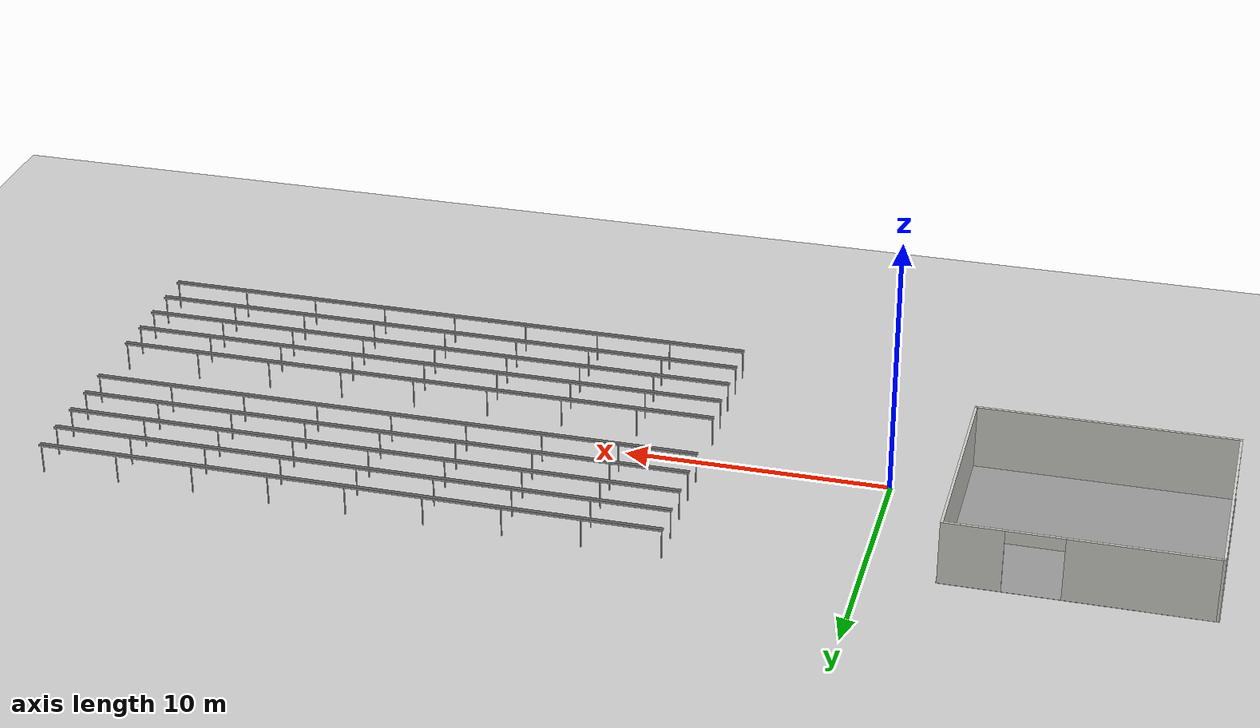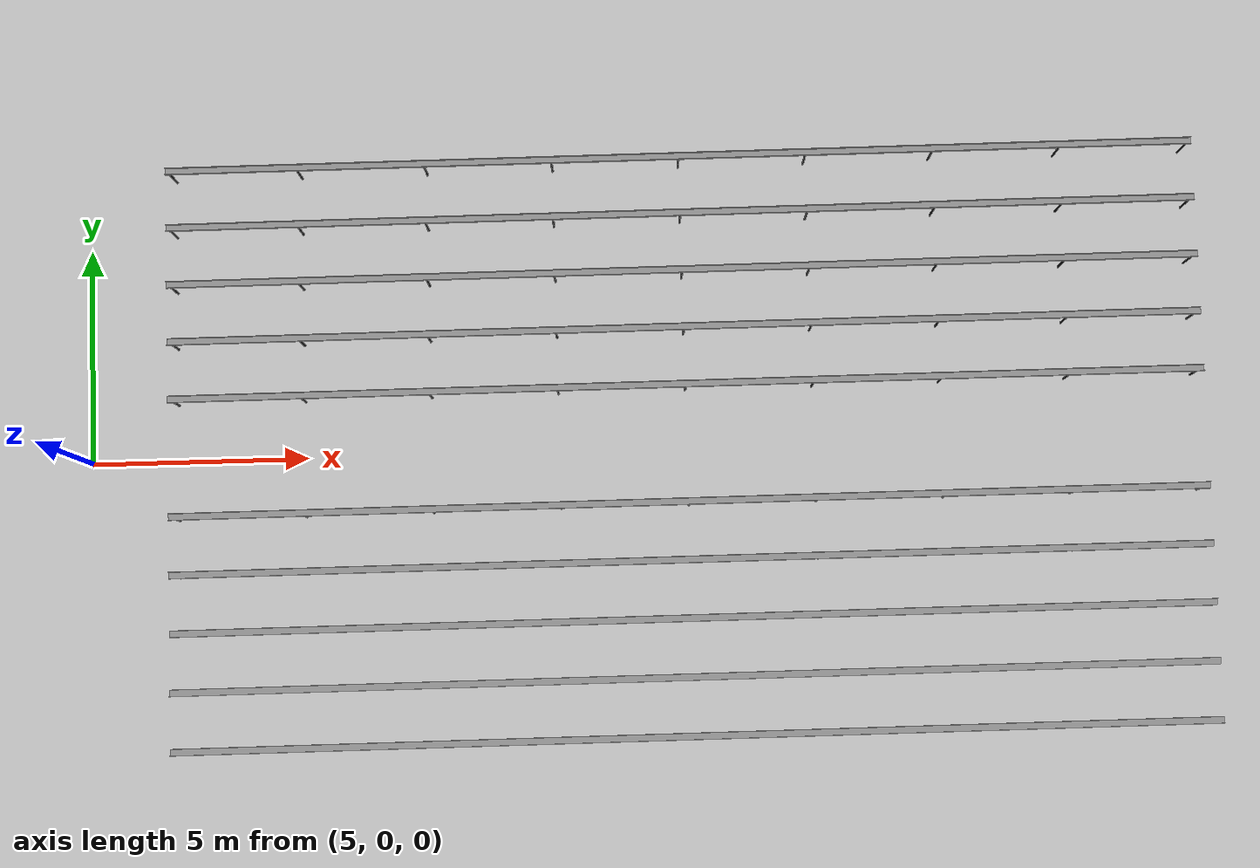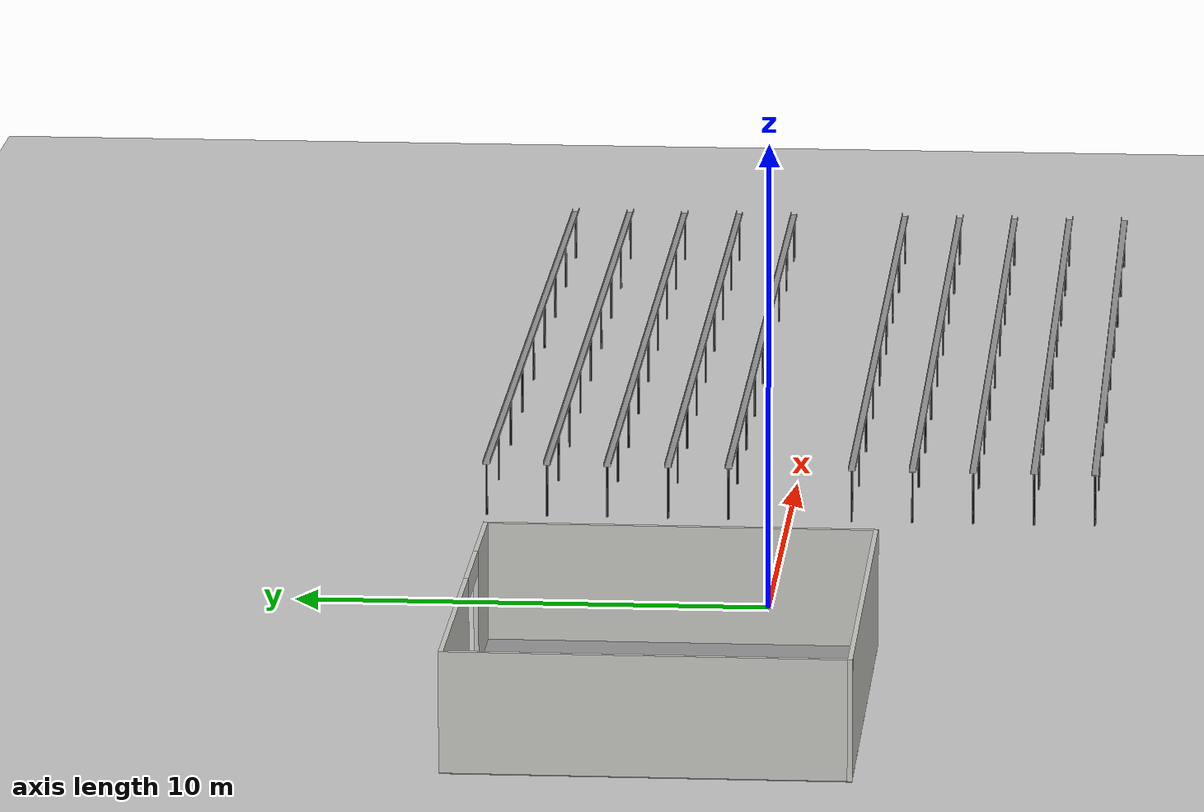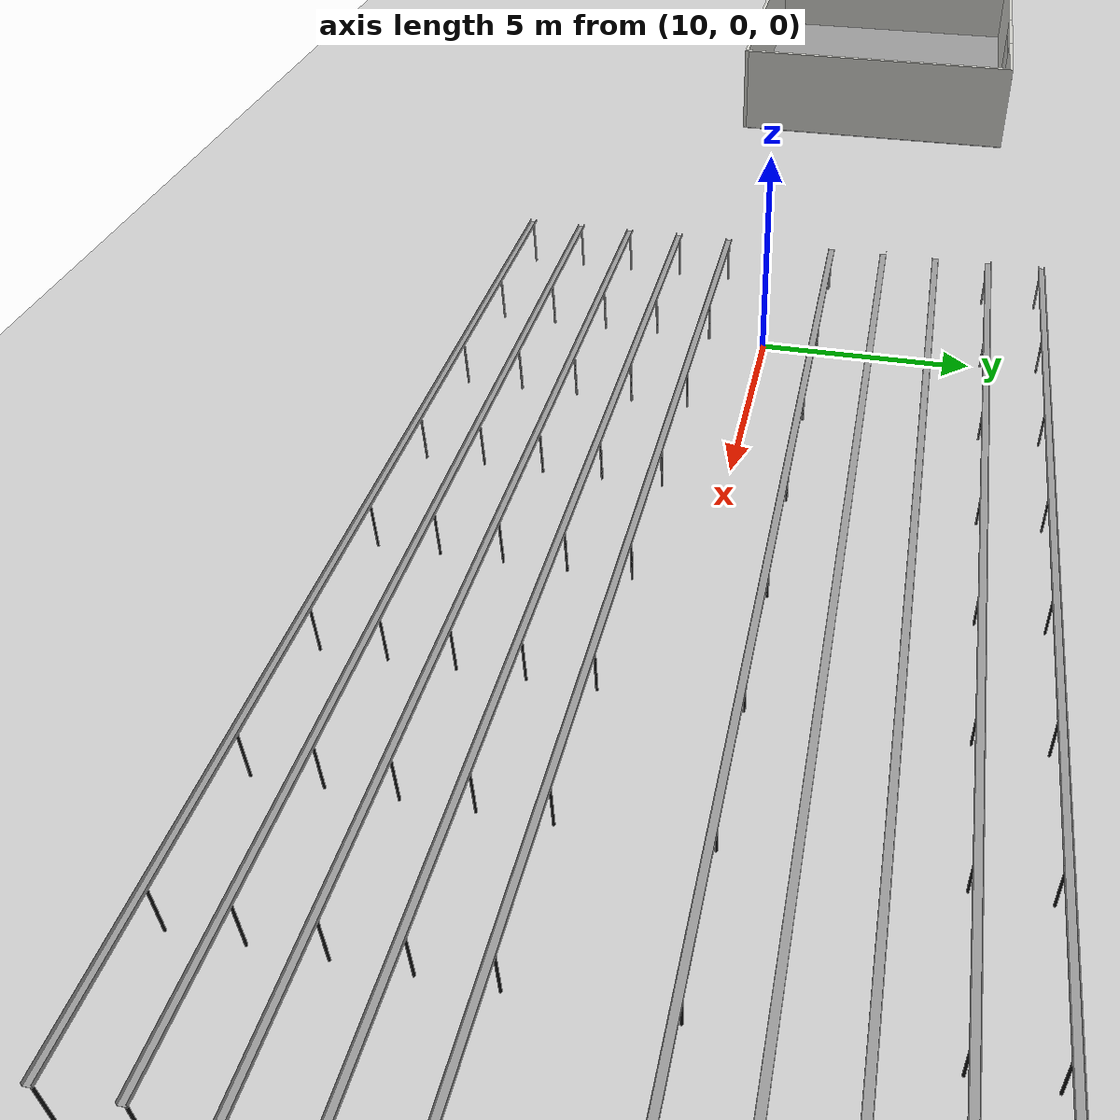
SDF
<sdf version="1.6">
 <world name="default">
  <physics name="default_physics" default="0" type="ode">
   <real_time_update_rate>200</real_time_update_rate>
   <real_time_factor>1</real_time_factor>
   <max_step_size>0.005</max_step_size>
  </physics>
  <model name="pole_0">
   <static>1</static>
   <pose>7 -6.64 0.575 0 -0 0</pose>
   <link name="link">
    <collision name="collision">
     <geometry><cylinder><length>1.15</length><radius>0.025</radius></cylinder></geometry>
    </collision>
    <visual name="visual">
     <geometry><cylinder><length>1.15</length><radius>0.025</radius></cylinder></geometry>
     <material>
      <script><uri>file://media/materials/scripts/gazebo.material</uri><name>Gazebo/Chrome</name></script>
      <shader type="vertex"><normal_map>__default__</normal_map></shader>
      <emissive>0.1 0.1 0.1 1</emissive>
      <specular>0.01 0.01 0.01 1</specular>
      <ambient>0.5 0.5 0.5 1</ambient>
      <diffuse>0.05 0.05 0.05 1</diffuse>
     </material>
    </visual>
   </link>
  </model>
  <model name="pole_1">
   <static>1</static>
   <pose>7 -5.32 0.575 0 -0 0</pose>
   <link name="link">
    <collision name="collision">
     <geometry><cylinder><length>1.15</length><radius>0.025</radius></cylinder></geometry>
    </collision>
    <visual name="visual">
     <geometry><cylinder><length>1.15</length><radius>0.025</radius></cylinder></geometry>
     <material>
      <script><uri>file://media/materials/scripts/gazebo.material</uri><name>Gazebo/Chrome</name></script>
      <shader type="vertex"><normal_map>__default__</normal_map></shader>
      <emissive>0.1 0.1 0.1 1</emissive>
      <specular>0.01 0.01 0.01 1</specular>
      <ambient>0.5 0.5 0.5 1</ambient>
      <diffuse>0.05 0.05 0.05 1</diffuse>
     </material>
    </visual>
   </link>
  </model>
  <model name="pole_2">
   <static>1</static>
   <pose>7 -4 0.575 0 -0 0</pose>
   <link name="link">
    <collision name="collision">
     <geometry><cylinder><length>1.15</length><radius>0.025</radius></cylinder></geometry>
    </collision>
    <visual name="visual">
     <geometry><cylinder><length>1.15</length><radius>0.025</radius></cylinder></geometry>
     <material>
      <script><uri>file://media/materials/scripts/gazebo.material</uri><name>Gazebo/Chrome</name></script>
      <shader type="vertex"><normal_map>__default__</normal_map></shader>
      <emissive>0.1 0.1 0.1 1</emissive>
      <specular>0.01 0.01 0.01 1</specular>
      <ambient>0.5 0.5 0.5 1</ambient>
      <diffuse>0.05 0.05 0.05 1</diffuse>
     </material>
    </visual>
   </link>
  </model>
  <model name="pole_3">
   <static>1</static>
   <pose>7 -2.68 0.575 0 -0 0</pose>
   <link name="link">
    <collision name="collision">
     <geometry><cylinder><length>1.15</length><radius>0.025</radius></cylinder></geometry>
    </collision>
    <visual name="visual">
     <geometry><cylinder><length>1.15</length><radius>0.025</radius></cylinder></geometry>
     <material>
      <script><uri>file://media/materials/scripts/gazebo.material</uri><name>Gazebo/Chrome</name></script>
      <shader type="vertex"><normal_map>__default__</normal_map></shader>
      <emissive>0.1 0.1 0.1 1</emissive>
      <specular>0.01 0.01 0.01 1</specular>
      <ambient>0.5 0.5 0.5 1</ambient>
      <diffuse>0.05 0.05 0.05 1</diffuse>
     </material>
    </visual>
   </link>
  </model>
  <model name="pole_4">
   <static>1</static>
   <pose>7 -1.36 0.575 0 -0 0</pose>
   <link name="link">
    <collision name="collision">
     <geometry><cylinder><length>1.15</length><radius>0.025</radius></cylinder></geometry>
    </collision>
    <visual name="visual">
     <geometry><cylinder><length>1.15</length><radius>0.025</radius></cylinder></geometry>
     <material>
      <script><uri>file://media/materials/scripts/gazebo.material</uri><name>Gazebo/Chrome</name></script>
      <shader type="vertex"><normal_map>__default__</normal_map></shader>
      <emissive>0.1 0.1 0.1 1</emissive>
      <specular>0.01 0.01 0.01 1</specular>
      <ambient>0.5 0.5 0.5 1</ambient>
      <diffuse>0.05 0.05 0.05 1</diffuse>
     </material>
    </visual>
   </link>
  </model>
  <model name="pole_5">
   <static>1</static>
   <pose>9.94 -6.64 0.575 0 -0 0</pose>
   <link name="link">
    <collision name="collision">
     <geometry><cylinder><length>1.15</length><radius>0.025</radius></cylinder></geometry>
    </collision>
    <visual name="visual">
     <geometry><cylinder><length>1.15</length><radius>0.025</radius></cylinder></geometry>
     <material>
      <script><uri>file://media/materials/scripts/gazebo.material</uri><name>Gazebo/Chrome</name></script>
      <shader type="vertex"><normal_map>__default__</normal_map></shader>
      <emissive>0.1 0.1 0.1 1</emissive>
      <specular>0.01 0.01 0.01 1</specular>
      <ambient>0.5 0.5 0.5 1</ambient>
      <diffuse>0.05 0.05 0.05 1</diffuse>
     </material>
    </visual>
   </link>
  </model>
  <model name="pole_6">
   <static>1</static>
   <pose>9.94 -5.32 0.575 0 -0 0</pose>
   <link name="link">
    <collision name="collision">
     <geometry><cylinder><length>1.15</length><radius>0.025</radius></cylinder></geometry>
    </collision>
    <visual name="visual">
     <geometry><cylinder><length>1.15</length><radius>0.025</radius></cylinder></geometry>
     <material>
      <script><uri>file://media/materials/scripts/gazebo.material</uri><name>Gazebo/Chrome</name></script>
      <shader type="vertex"><normal_map>__default__</normal_map></shader>
      <emissive>0.1 0.1 0.1 1</emissive>
      <specular>0.01 0.01 0.01 1</specular>
      <ambient>0.5 0.5 0.5 1</ambient>
      <diffuse>0.05 0.05 0.05 1</diffuse>
     </material>
    </visual>
   </link>
  </model>
  <model name="pole_7">
   <static>1</static>
   <pose>9.94 -4 0.575 0 -0 0</pose>
   <link name="link">
    <collision name="collision">
     <geometry><cylinder><length>1.15</length><radius>0.025</radius></cylinder></geometry>
    </collision>
    <visual name="visual">
     <geometry><cylinder><length>1.15</length><radius>0.025</radius></cylinder></geometry>
     <material>
      <script><uri>file://media/materials/scripts/gazebo.material</uri><name>Gazebo/Chrome</name></script>
      <shader type="vertex"><normal_map>__default__</normal_map></shader>
      <emissive>0.1 0.1 0.1 1</emissive>
      <specular>0.01 0.01 0.01 1</specular>
      <ambient>0.5 0.5 0.5 1</ambient>
      <diffuse>0.05 0.05 0.05 1</diffuse>
     </material>
    </visual>
   </link>
  </model>
  <model name="pole_8">
   <static>1</static>
   <pose>9.94 -2.68 0.575 0 -0 0</pose>
   <link name="link">
    <collision name="collision">
     <geometry><cylinder><length>1.15</length><radius>0.025</radius></cylinder></geometry>
    </collision>
    <visual name="visual">
     <geometry><cylinder><length>1.15</length><radius>0.025</radius></cylinder></geometry>
     <material>
      <script><uri>file://media/materials/scripts/gazebo.material</uri><name>Gazebo/Chrome</name></script>
      <shader type="vertex"><normal_map>__default__</normal_map></shader>
      <emissive>0.1 0.1 0.1 1</emissive>
      <specular>0.01 0.01 0.01 1</specular>
      <ambient>0.5 0.5 0.5 1</ambient>
      <diffuse>0.05 0.05 0.05 1</diffuse>
     </material>
    </visual>
   </link>
  </model>
  <model name="pole_9">
   <static>1</static>
   <pose>9.94 -1.36 0.575 0 -0 0</pose>
   <link name="link">
    <collision name="collision">
     <geometry><cylinder><length>1.15</length><radius>0.025</radius></cylinder></geometry>
    </collision>
    <visual name="visual">
     <geometry><cylinder><length>1.15</length><radius>0.025</radius></cylinder></geometry>
     <material>
      <script><uri>file://media/materials/scripts/gazebo.material</uri><name>Gazebo/Chrome</name></script>
      <shader type="vertex"><normal_map>__default__</normal_map></shader>
      <emissive>0.1 0.1 0.1 1</emissive>
      <specular>0.01 0.01 0.01 1</specular>
      <ambient>0.5 0.5 0.5 1</ambient>
      <diffuse>0.05 0.05 0.05 1</diffuse>
     </material>
    </visual>
   </link>
  </model>
  <model name="pole_10">
   <static>1</static>
   <pose>12.88 -6.64 0.575 0 -0 0</pose>
   <link name="link">
    <collision name="collision">
     <geometry><cylinder><length>1.15</length><radius>0.025</radius></cylinder></geometry>
    </collision>
    <visual name="visual">
     <geometry><cylinder><length>1.15</length><radius>0.025</radius></cylinder></geometry>
     <material>
      <script><uri>file://media/materials/scripts/gazebo.material</uri><name>Gazebo/Chrome</name></script>
      <shader type="vertex"><normal_map>__default__</normal_map></shader>
      <emissive>0.1 0.1 0.1 1</emissive>
      <specular>0.01 0.01 0.01 1</specular>
      <ambient>0.5 0.5 0.5 1</ambient>
      <diffuse>0.05 0.05 0.05 1</diffuse>
     </material>
    </visual>
   </link>
  </model>
  <model name="pole_11">
   <static>1</static>
   <pose>12.88 -5.32 0.575 0 -0 0</pose>
   <link name="link">
    <collision name="collision">
     <geometry><cylinder><length>1.15</length><radius>0.025</radius></cylinder></geometry>
    </collision>
    <visual name="visual">
     <geometry><cylinder><length>1.15</length><radius>0.025</radius></cylinder></geometry>
     <material>
      <script><uri>file://media/materials/scripts/gazebo.material</uri><name>Gazebo/Chrome</name></script>
      <shader type="vertex"><normal_map>__default__</normal_map></shader>
      <emissive>0.1 0.1 0.1 1</emissive>
      <specular>0.01 0.01 0.01 1</specular>
      <ambient>0.5 0.5 0.5 1</ambient>
      <diffuse>0.05 0.05 0.05 1</diffuse>
     </material>
    </visual>
   </link>
  </model>
  <model name="pole_12">
   <static>1</static>
   <pose>12.88 -4 0.575 0 -0 0</pose>
   <link name="link">
    <collision name="collision">
     <geometry><cylinder><length>1.15</length><radius>0.025</radius></cylinder></geometry>
    </collision>
    <visual name="visual">
     <geometry><cylinder><length>1.15</length><radius>0.025</radius></cylinder></geometry>
     <material>
      <script><uri>file://media/materials/scripts/gazebo.material</uri><name>Gazebo/Chrome</name></script>
      <shader type="vertex"><normal_map>__default__</normal_map></shader>
      <emissive>0.1 0.1 0.1 1</emissive>
      <specular>0.01 0.01 0.01 1</specular>
      <ambient>0.5 0.5 0.5 1</ambient>
      <diffuse>0.05 0.05 0.05 1</diffuse>
     </material>
    </visual>
   </link>
  </model>
  <model name="pole_13">
   <static>1</static>
   <pose>12.88 -2.68 0.575 0 -0 0</pose>
   <link name="link">
    <collision name="collision">
     <geometry><cylinder><length>1.15</length><radius>0.025</radius></cylinder></geometry>
    </collision>
    <visual name="visual">
     <geometry><cylinder><length>1.15</length><radius>0.025</radius></cylinder></geometry>
     <material>
      <script><uri>file://media/materials/scripts/gazebo.material</uri><name>Gazebo/Chrome</name></script>
      <shader type="vertex"><normal_map>__default__</normal_map></shader>
      <emissive>0.1 0.1 0.1 1</emissive>
      <specular>0.01 0.01 0.01 1</specular>
      <ambient>0.5 0.5 0.5 1</ambient>
      <diffuse>0.05 0.05 0.05 1</diffuse>
     </material>
    </visual>
   </link>
  </model>
  <model name="pole_14">
   <static>1</static>
   <pose>12.88 -1.36 0.575 0 -0 0</pose>
   <link name="link">
    <collision name="collision">
     <geometry><cylinder><length>1.15</length><radius>0.025</radius></cylinder></geometry>
    </collision>
    <visual name="visual">
     <geometry><cylinder><length>1.15</length><radius>0.025</radius></cylinder></geometry>
     <material>
      <script><uri>file://media/materials/scripts/gazebo.material</uri><name>Gazebo/Chrome</name></script>
      <shader type="vertex"><normal_map>__default__</normal_map></shader>
      <emissive>0.1 0.1 0.1 1</emissive>
      <specular>0.01 0.01 0.01 1</specular>
      <ambient>0.5 0.5 0.5 1</ambient>
      <diffuse>0.05 0.05 0.05 1</diffuse>
     </material>
    </visual>
   </link>
  </model>
  <model name="pole_15">
   <static>1</static>
   <pose>15.82 -6.64 0.575 0 -0 0</pose>
   <link name="link">
    <collision name="collision">
     <geometry><cylinder><length>1.15</length><radius>0.025</radius></cylinder></geometry>
    </collision>
    <visual name="visual">
     <geometry><cylinder><length>1.15</length><radius>0.025</radius></cylinder></geometry>
     <material>
      <script><uri>file://media/materials/scripts/gazebo.material</uri><name>Gazebo/Chrome</name></script>
      <shader type="vertex"><normal_map>__default__</normal_map></shader>
      <emissive>0.1 0.1 0.1 1</emissive>
      <specular>0.01 0.01 0.01 1</specular>
      <ambient>0.5 0.5 0.5 1</ambient>
      <diffuse>0.05 0.05 0.05 1</diffuse>
     </material>
    </visual>
   </link>
  </model>
  <model name="pole_16">
   <static>1</static>
   <pose>15.82 -5.32 0.575 0 -0 0</pose>
   <link name="link">
    <collision name="collision">
     <geometry><cylinder><length>1.15</length><radius>0.025</radius></cylinder></geometry>
    </collision>
    <visual name="visual">
     <geometry><cylinder><length>1.15</length><radius>0.025</radius></cylinder></geometry>
     <material>
      <script><uri>file://media/materials/scripts/gazebo.material</uri><name>Gazebo/Chrome</name></script>
      <shader type="vertex"><normal_map>__default__</normal_map></shader>
      <emissive>0.1 0.1 0.1 1</emissive>
      <specular>0.01 0.01 0.01 1</specular>
      <ambient>0.5 0.5 0.5 1</ambient>
      <diffuse>0.05 0.05 0.05 1</diffuse>
     </material>
    </visual>
   </link>
  </model>
  <model name="pole_17">
   <static>1</static>
   <pose>15.82 -4 0.575 0 -0 0</pose>
   <link name="link">
    <collision name="collision">
     <geometry><cylinder><length>1.15</length><radius>0.025</radius></cylinder></geometry>
    </collision>
    <visual name="visual">
     <geometry><cylinder><length>1.15</length><radius>0.025</radius></cylinder></geometry>
     <material>
      <script><uri>file://media/materials/scripts/gazebo.material</uri><name>Gazebo/Chrome</name></script>
      <shader type="vertex"><normal_map>__default__</normal_map></shader>
      <emissive>0.1 0.1 0.1 1</emissive>
      <specular>0.01 0.01 0.01 1</specular>
      <ambient>0.5 0.5 0.5 1</ambient>
      <diffuse>0.05 0.05 0.05 1</diffuse>
     </material>
    </visual>
   </link>
  </model>
  <model name="pole_18">
   <static>1</static>
   <pose>15.82 -2.68 0.575 0 -0 0</pose>
   <link name="link">
    <collision name="collision">
     <geometry><cylinder><length>1.15</length><radius>0.025</radius></cylinder></geometry>
    </collision>
    <visual name="visual">
     <geometry><cylinder><length>1.15</length><radius>0.025</radius></cylinder></geometry>
     <material>
      <script><uri>file://media/materials/scripts/gazebo.material</uri><name>Gazebo/Chrome</name></script>
      <shader type="vertex"><normal_map>__default__</normal_map></shader>
      <emissive>0.1 0.1 0.1 1</emissive>
      <specular>0.01 0.01 0.01 1</specular>
      <ambient>0.5 0.5 0.5 1</ambient>
      <diffuse>0.05 0.05 0.05 1</diffuse>
     </material>
    </visual>
   </link>
  </model>
  <model name="pole_19">
   <static>1</static>
   <pose>15.82 -1.36 0.575 0 -0 0</pose>
   <link name="link">
    <collision name="collision">
     <geometry><cylinder><length>1.15</length><radius>0.025</radius></cylinder></geometry>
    </collision>
    <visual name="visual">
     <geometry><cylinder><length>1.15</length><radius>0.025</radius></cylinder></geometry>
     <material>
      <script><uri>file://media/materials/scripts/gazebo.material</uri><name>Gazebo/Chrome</name></script>
      <shader type="vertex"><normal_map>__default__</normal_map></shader>
      <emissive>0.1 0.1 0.1 1</emissive>
      <specular>0.01 0.01 0.01 1</specular>
      <ambient>0.5 0.5 0.5 1</ambient>
      <diffuse>0.05 0.05 0.05 1</diffuse>
     </material>
    </visual>
   </link>
  </model>
  <model name="pole_20">
   <static>1</static>
   <pose>18.76 -6.64 0.575 0 -0 0</pose>
   <link name="link">
    <collision name="collision">
     <geometry><cylinder><length>1.15</length><radius>0.025</radius></cylinder></geometry>
    </collision>
    <visual name="visual">
     <geometry><cylinder><length>1.15</length><radius>0.025</radius></cylinder></geometry>
     <material>
      <script><uri>file://media/materials/scripts/gazebo.material</uri><name>Gazebo/Chrome</name></script>
      <shader type="vertex"><normal_map>__default__</normal_map></shader>
      <emissive>0.1 0.1 0.1 1</emissive>
      <specular>0.01 0.01 0.01 1</specular>
      <ambient>0.5 0.5 0.5 1</ambient>
      <diffuse>0.05 0.05 0.05 1</diffuse>
     </material>
    </visual>
   </link>
  </model>
  <model name="pole_21">
   <static>1</static>
   <pose>18.76 -5.32 0.575 0 -0 0</pose>
   <link name="link">
    <collision name="collision">
     <geometry><cylinder><length>1.15</length><radius>0.025</radius></cylinder></geometry>
    </collision>
    <visual name="visual">
     <geometry><cylinder><length>1.15</length><radius>0.025</radius></cylinder></geometry>
     <material>
      <script><uri>file://media/materials/scripts/gazebo.material</uri><name>Gazebo/Chrome</name></script>
      <shader type="vertex"><normal_map>__default__</normal_map></shader>
      <emissive>0.1 0.1 0.1 1</emissive>
      <specular>0.01 0.01 0.01 1</specular>
      <ambient>0.5 0.5 0.5 1</ambient>
      <diffuse>0.05 0.05 0.05 1</diffuse>
     </material>
    </visual>
   </link>
  </model>
  <model name="pole_22">
   <static>1</static>
   <pose>18.76 -4 0.575 0 -0 0</pose>
   <link name="link">
    <collision name="collision">
     <geometry><cylinder><length>1.15</length><radius>0.025</radius></cylinder></geometry>
    </collision>
    <visual name="visual">
     <geometry><cylinder><length>1.15</length><radius>0.025</radius></cylinder></geometry>
     <material>
      <script><uri>file://media/materials/scripts/gazebo.material</uri><name>Gazebo/Chrome</name></script>
      <shader type="vertex"><normal_map>__default__</normal_map></shader>
      <emissive>0.1 0.1 0.1 1</emissive>
      <specular>0.01 0.01 0.01 1</specular>
      <ambient>0.5 0.5 0.5 1</ambient>
      <diffuse>0.05 0.05 0.05 1</diffuse>
     </material>
    </visual>
   </link>
  </model>
  <model name="pole_23">
   <static>1</static>
   <pose>18.76 -2.68 0.575 0 -0 0</pose>
   <link name="link">
    <collision name="collision">
     <geometry><cylinder><length>1.15</length><radius>0.025</radius></cylinder></geometry>
    </collision>
    <visual name="visual">
     <geometry><cylinder><length>1.15</length><radius>0.025</radius></cylinder></geometry>
     <material>
      <script><uri>file://media/materials/scripts/gazebo.material</uri><name>Gazebo/Chrome</name></script>
      <shader type="vertex"><normal_map>__default__</normal_map></shader>
      <emissive>0.1 0.1 0.1 1</emissive>
      <specular>0.01 0.01 0.01 1</specular>
      <ambient>0.5 0.5 0.5 1</ambient>
      <diffuse>0.05 0.05 0.05 1</diffuse>
     </material>
    </visual>
   </link>
  </model>
  <model name="pole_24">
   <static>1</static>
   <pose>18.76 -1.36 0.575 0 -0 0</pose>
   <link name="link">
    <collision name="collision">
     <geometry><cylinder><length>1.15</length><radius>0.025</radius></cylinder></geometry>
    </collision>
    <visual name="visual">
     <geometry><cylinder><length>1.15</length><radius>0.025</radius></cylinder></geometry>
     <material>
      <script><uri>file://media/materials/scripts/gazebo.material</uri><name>Gazebo/Chrome</name></script>
      <shader type="vertex"><normal_map>__default__</normal_map></shader>
      <emissive>0.1 0.1 0.1 1</emissive>
      <specular>0.01 0.01 0.01 1</specular>
      <ambient>0.5 0.5 0.5 1</ambient>
      <diffuse>0.05 0.05 0.05 1</diffuse>
     </material>
    </visual>
   </link>
  </model>
  <model name="pole_25">
   <static>1</static>
   <pose>21.7 -6.64 0.575 0 -0 0</pose>
   <link name="link">
    <collision name="collision">
     <geometry><cylinder><length>1.15</length><radius>0.025</radius></cylinder></geometry>
    </collision>
    <visual name="visual">
     <geometry><cylinder><length>1.15</length><radius>0.025</radius></cylinder></geometry>
     <material>
      <script><uri>file://media/materials/scripts/gazebo.material</uri><name>Gazebo/Chrome</name></script>
      <shader type="vertex"><normal_map>__default__</normal_map></shader>
      <emissive>0.1 0.1 0.1 1</emissive>
      <specular>0.01 0.01 0.01 1</specular>
      <ambient>0.5 0.5 0.5 1</ambient>
      <diffuse>0.05 0.05 0.05 1</diffuse>
     </material>
    </visual>
   </link>
  </model>
  <model name="pole_26">
   <static>1</static>
   <pose>21.7 -5.32 0.575 0 -0 0</pose>
   <link name="link">
    <collision name="collision">
     <geometry><cylinder><length>1.15</length><radius>0.025</radius></cylinder></geometry>
    </collision>
    <visual name="visual">
     <geometry><cylinder><length>1.15</length><radius>0.025</radius></cylinder></geometry>
     <material>
      <script><uri>file://media/materials/scripts/gazebo.material</uri><name>Gazebo/Chrome</name></script>
      <shader type="vertex"><normal_map>__default__</normal_map></shader>
      <emissive>0.1 0.1 0.1 1</emissive>
      <specular>0.01 0.01 0.01 1</specular>
      <ambient>0.5 0.5 0.5 1</ambient>
      <diffuse>0.05 0.05 0.05 1</diffuse>
     </material>
    </visual>
   </link>
  </model>
  <model name="pole_27">
   <static>1</static>
   <pose>21.7 -4 0.575 0 -0 0</pose>
   <link name="link">
    <collision name="collision">
     <geometry><cylinder><length>1.15</length><radius>0.025</radius></cylinder></geometry>
    </collision>
    <visual name="visual">
     <geometry><cylinder><length>1.15</length><radius>0.025</radius></cylinder></geometry>
     <material>
      <script><uri>file://media/materials/scripts/gazebo.material</uri><name>Gazebo/Chrome</name></script>
      <shader type="vertex"><normal_map>__default__</normal_map></shader>
      <emissive>0.1 0.1 0.1 1</emissive>
      <specular>0.01 0.01 0.01 1</specular>
      <ambient>0.5 0.5 0.5 1</ambient>
      <diffuse>0.05 0.05 0.05 1</diffuse>
     </material>
    </visual>
   </link>
  </model>
  <model name="pole_28">
   <static>1</static>
   <pose>21.7 -2.68 0.575 0 -0 0</pose>
   <link name="link">
    <collision name="collision">
     <geometry><cylinder><length>1.15</length><radius>0.025</radius></cylinder></geometry>
    </collision>
    <visual name="visual">
     <geometry><cylinder><length>1.15</length><radius>0.025</radius></cylinder></geometry>
     <material>
      <script><uri>file://media/materials/scripts/gazebo.material</uri><name>Gazebo/Chrome</name></script>
      <shader type="vertex"><normal_map>__default__</normal_map></shader>
      <emissive>0.1 0.1 0.1 1</emissive>
      <specular>0.01 0.01 0.01 1</specular>
      <ambient>0.5 0.5 0.5 1</ambient>
      <diffuse>0.05 0.05 0.05 1</diffuse>
     </material>
    </visual>
   </link>
  </model>
  <model name="pole_29">
   <static>1</static>
   <pose>21.7 -1.36 0.575 0 -0 0</pose>
   <link name="link">
    <collision name="collision">
     <geometry><cylinder><length>1.15</length><radius>0.025</radius></cylinder></geometry>
    </collision>
    <visual name="visual">
     <geometry><cylinder><length>1.15</length><radius>0.025</radius></cylinder></geometry>
     <material>
      <script><uri>file://media/materials/scripts/gazebo.material</uri><name>Gazebo/Chrome</name></script>
      <shader type="vertex"><normal_map>__default__</normal_map></shader>
      <emissive>0.1 0.1 0.1 1</emissive>
      <specular>0.01 0.01 0.01 1</specular>
      <ambient>0.5 0.5 0.5 1</ambient>
      <diffuse>0.05 0.05 0.05 1</diffuse>
     </material>
    </visual>
   </link>
  </model>
  <model name="pole_30">
   <static>1</static>
   <pose>24.64 -6.64 0.575 0 -0 0</pose>
   <link name="link">
    <collision name="collision">
     <geometry><cylinder><length>1.15</length><radius>0.025</radius></cylinder></geometry>
    </collision>
    <visual name="visual">
     <geometry><cylinder><length>1.15</length><radius>0.025</radius></cylinder></geometry>
     <material>
      <script><uri>file://media/materials/scripts/gazebo.material</uri><name>Gazebo/Chrome</name></script>
      <shader type="vertex"><normal_map>__default__</normal_map></shader>
      <emissive>0.1 0.1 0.1 1</emissive>
      <specular>0.01 0.01 0.01 1</specular>
      <ambient>0.5 0.5 0.5 1</ambient>
      <diffuse>0.05 0.05 0.05 1</diffuse>
     </material>
    </visual>
   </link>
  </model>
  <model name="pole_31">
   <static>1</static>
   <pose>24.64 -5.32 0.575 0 -0 0</pose>
   <link name="link">
    <collision name="collision">
     <geometry><cylinder><length>1.15</length><radius>0.025</radius></cylinder></geometry>
    </collision>
    <visual name="visual">
     <geometry><cylinder><length>1.15</length><radius>0.025</radius></cylinder></geometry>
     <material>
      <script><uri>file://media/materials/scripts/gazebo.material</uri><name>Gazebo/Chrome</name></script>
      <shader type="vertex"><normal_map>__default__</normal_map></shader>
      <emissive>0.1 0.1 0.1 1</emissive>
      <specular>0.01 0.01 0.01 1</specular>
      <ambient>0.5 0.5 0.5 1</ambient>
      <diffuse>0.05 0.05 0.05 1</diffuse>
     </material>
    </visual>
   </link>
  </model>
  <model name="pole_32">
   <static>1</static>
   <pose>24.64 -4 0.575 0 -0 0</pose>
   <link name="link">
    <collision name="collision">
     <geometry><cylinder><length>1.15</length><radius>0.025</radius></cylinder></geometry>
    </collision>
    <visual name="visual">
     <geometry><cylinder><length>1.15</length><radius>0.025</radius></cylinder></geometry>
     <material>
      <script><uri>file://media/materials/scripts/gazebo.material</uri><name>Gazebo/Chrome</name></script>
      <shader type="vertex"><normal_map>__default__</normal_map></shader>
      <emissive>0.1 0.1 0.1 1</emissive>
      <specular>0.01 0.01 0.01 1</specular>
      <ambient>0.5 0.5 0.5 1</ambient>
      <diffuse>0.05 0.05 0.05 1</diffuse>
     </material>
    </visual>
   </link>
  </model>
  <model name="pole_33">
   <static>1</static>
   <pose>24.64 -2.68 0.575 0 -0 0</pose>
   <link name="link">
    <collision name="collision">
     <geometry><cylinder><length>1.15</length><radius>0.025</radius></cylinder></geometry>
    </collision>
    <visual name="visual">
     <geometry><cylinder><length>1.15</length><radius>0.025</radius></cylinder></geometry>
     <material>
      <script><uri>file://media/materials/scripts/gazebo.material</uri><name>Gazebo/Chrome</name></script>
      <shader type="vertex"><normal_map>__default__</normal_map></shader>
      <emissive>0.1 0.1 0.1 1</emissive>
      <specular>0.01 0.01 0.01 1</specular>
      <ambient>0.5 0.5 0.5 1</ambient>
      <diffuse>0.05 0.05 0.05 1</diffuse>
     </material>
    </visual>
   </link>
  </model>
  <model name="pole_34">
   <static>1</static>
   <pose>24.64 -1.36 0.575 0 -0 0</pose>
   <link name="link">
    <collision name="collision">
     <geometry><cylinder><length>1.15</length><radius>0.025</radius></cylinder></geometry>
    </collision>
    <visual name="visual">
     <geometry><cylinder><length>1.15</length><radius>0.025</radius></cylinder></geometry>
     <material>
      <script><uri>file://media/materials/scripts/gazebo.material</uri><name>Gazebo/Chrome</name></script>
      <shader type="vertex"><normal_map>__default__</normal_map></shader>
      <emissive>0.1 0.1 0.1 1</emissive>
      <specular>0.01 0.01 0.01 1</specular>
      <ambient>0.5 0.5 0.5 1</ambient>
      <diffuse>0.05 0.05 0.05 1</diffuse>
     </material>
    </visual>
   </link>
  </model>
  <model name="pole_35">
   <static>1</static>
   <pose>27.58 -6.64 0.575 0 -0 0</pose>
   <link name="link">
    <collision name="collision">
     <geometry><cylinder><length>1.15</length><radius>0.025</radius></cylinder></geometry>
    </collision>
    <visual name="visual">
     <geometry><cylinder><length>1.15</length><radius>0.025</radius></cylinder></geometry>
     <material>
      <script><uri>file://media/materials/scripts/gazebo.material</uri><name>Gazebo/Chrome</name></script>
      <shader type="vertex"><normal_map>__default__</normal_map></shader>
      <emissive>0.1 0.1 0.1 1</emissive>
      <specular>0.01 0.01 0.01 1</specular>
      <ambient>0.5 0.5 0.5 1</ambient>
      <diffuse>0.05 0.05 0.05 1</diffuse>
     </material>
    </visual>
   </link>
  </model>
  <model name="pole_36">
   <static>1</static>
   <pose>27.58 -5.32 0.575 0 -0 0</pose>
   <link name="link">
    <collision name="collision">
     <geometry><cylinder><length>1.15</length><radius>0.025</radius></cylinder></geometry>
    </collision>
    <visual name="visual">
     <geometry><cylinder><length>1.15</length><radius>0.025</radius></cylinder></geometry>
     <material>
      <script><uri>file://media/materials/scripts/gazebo.material</uri><name>Gazebo/Chrome</name></script>
      <shader type="vertex"><normal_map>__default__</normal_map></shader>
      <emissive>0.1 0.1 0.1 1</emissive>
      <specular>0.01 0.01 0.01 1</specular>
      <ambient>0.5 0.5 0.5 1</ambient>
      <diffuse>0.05 0.05 0.05 1</diffuse>
     </material>
    </visual>
   </link>
  </model>
  <model name="pole_37">
   <static>1</static>
   <pose>27.58 -4 0.575 0 -0 0</pose>
   <link name="link">
    <collision name="collision">
     <geometry><cylinder><length>1.15</length><radius>0.025</radius></cylinder></geometry>
    </collision>
    <visual name="visual">
     <geometry><cylinder><length>1.15</length><radius>0.025</radius></cylinder></geometry>
     <material>
      <script><uri>file://media/materials/scripts/gazebo.material</uri><name>Gazebo/Chrome</name></script>
      <shader type="vertex"><normal_map>__default__</normal_map></shader>
      <emissive>0.1 0.1 0.1 1</emissive>
      <specular>0.01 0.01 0.01 1</specular>
      <ambient>0.5 0.5 0.5 1</ambient>
      <diffuse>0.05 0.05 0.05 1</diffuse>
     </material>
    </visual>
   </link>
  </model>
  <model name="pole_38">
   <static>1</static>
   <pose>27.58 -2.68 0.575 0 -0 0</pose>
   <link name="link">
    <collision name="collision">
     <geometry><cylinder><length>1.15</length><radius>0.025</radius></cylinder></geometry>
    </collision>
    <visual name="visual">
     <geometry><cylinder><length>1.15</length><radius>0.025</radius></cylinder></geometry>
     <material>
      <script><uri>file://media/materials/scripts/gazebo.material</uri><name>Gazebo/Chrome</name></script>
      <shader type="vertex"><normal_map>__default__</normal_map></shader>
      <emissive>0.1 0.1 0.1 1</emissive>
      <specular>0.01 0.01 0.01 1</specular>
      <ambient>0.5 0.5 0.5 1</ambient>
      <diffuse>0.05 0.05 0.05 1</diffuse>
     </material>
    </visual>
   </link>
  </model>
  <model name="pole_39">
   <static>1</static>
   <pose>27.58 -1.36 0.575 0 -0 0</pose>
   <link name="link">
    <collision name="collision">
     <geometry><cylinder><length>1.15</length><radius>0.025</radius></cylinder></geometry>
    </collision>
    <visual name="visual">
     <geometry><cylinder><length>1.15</length><radius>0.025</radius></cylinder></geometry>
     <material>
      <script><uri>file://media/materials/scripts/gazebo.material</uri><name>Gazebo/Chrome</name></script>
      <shader type="vertex"><normal_map>__default__</normal_map></shader>
      <emissive>0.1 0.1 0.1 1</emissive>
      <specular>0.01 0.01 0.01 1</specular>
      <ambient>0.5 0.5 0.5 1</ambient>
      <diffuse>0.05 0.05 0.05 1</diffuse>
     </material>
    </visual>
   </link>
  </model>
  <model name="pole_40">
   <static>1</static>
   <pose>30.52 -6.64 0.575 0 -0 0</pose>
   <link name="link">
    <collision name="collision">
     <geometry><cylinder><length>1.15</length><radius>0.025</radius></cylinder></geometry>
    </collision>
    <visual name="visual">
     <geometry><cylinder><length>1.15</length><radius>0.025</radius></cylinder></geometry>
     <material>
      <script><uri>file://media/materials/scripts/gazebo.material</uri><name>Gazebo/Chrome</name></script>
      <shader type="vertex"><normal_map>__default__</normal_map></shader>
      <emissive>0.1 0.1 0.1 1</emissive>
      <specular>0.01 0.01 0.01 1</specular>
      <ambient>0.5 0.5 0.5 1</ambient>
      <diffuse>0.05 0.05 0.05 1</diffuse>
     </material>
    </visual>
   </link>
  </model>
  <model name="pole_41">
   <static>1</static>
   <pose>30.52 -5.32 0.575 0 -0 0</pose>
   <link name="link">
    <collision name="collision">
     <geometry><cylinder><length>1.15</length><radius>0.025</radius></cylinder></geometry>
    </collision>
    <visual name="visual">
     <geometry><cylinder><length>1.15</length><radius>0.025</radius></cylinder></geometry>
     <material>
      <script><uri>file://media/materials/scripts/gazebo.material</uri><name>Gazebo/Chrome</name></script>
      <shader type="vertex"><normal_map>__default__</normal_map></shader>
      <emissive>0.1 0.1 0.1 1</emissive>
      <specular>0.01 0.01 0.01 1</specular>
      <ambient>0.5 0.5 0.5 1</ambient>
      <diffuse>0.05 0.05 0.05 1</diffuse>
     </material>
    </visual>
   </link>
  </model>
  <model name="pole_42">
   <static>1</static>
   <pose>30.52 -4 0.575 0 -0 0</pose>
   <link name="link">
    <collision name="collision">
     <geometry><cylinder><length>1.15</length><radius>0.025</radius></cylinder></geometry>
    </collision>
    <visual name="visual">
     <geometry><cylinder><length>1.15</length><radius>0.025</radius></cylinder></geometry>
     <material>
      <script><uri>file://media/materials/scripts/gazebo.material</uri><name>Gazebo/Chrome</name></script>
      <shader type="vertex"><normal_map>__default__</normal_map></shader>
      <emissive>0.1 0.1 0.1 1</emissive>
      <specular>0.01 0.01 0.01 1</specular>
      <ambient>0.5 0.5 0.5 1</ambient>
      <diffuse>0.05 0.05 0.05 1</diffuse>
     </material>
    </visual>
   </link>
  </model>
  <model name="pole_43">
   <static>1</static>
   <pose>30.52 -2.68 0.575 0 -0 0</pose>
   <link name="link">
    <collision name="collision">
     <geometry><cylinder><length>1.15</length><radius>0.025</radius></cylinder></geometry>
    </collision>
    <visual name="visual">
     <geometry><cylinder><length>1.15</length><radius>0.025</radius></cylinder></geometry>
     <material>
      <script><uri>file://media/materials/scripts/gazebo.material</uri><name>Gazebo/Chrome</name></script>
      <shader type="vertex"><normal_map>__default__</normal_map></shader>
      <emissive>0.1 0.1 0.1 1</emissive>
      <specular>0.01 0.01 0.01 1</specular>
      <ambient>0.5 0.5 0.5 1</ambient>
      <diffuse>0.05 0.05 0.05 1</diffuse>
     </material>
    </visual>
   </link>
  </model>
  <model name="pole_44">
   <static>1</static>
   <pose>30.52 -1.36 0.575 0 -0 0</pose>
   <link name="link">
    <collision name="collision">
     <geometry><cylinder><length>1.15</length><radius>0.025</radius></cylinder></geometry>
    </collision>
    <visual name="visual">
     <geometry><cylinder><length>1.15</length><radius>0.025</radius></cylinder></geometry>
     <material>
      <script><uri>file://media/materials/scripts/gazebo.material</uri><name>Gazebo/Chrome</name></script>
      <shader type="vertex"><normal_map>__default__</normal_map></shader>
      <emissive>0.1 0.1 0.1 1</emissive>
      <specular>0.01 0.01 0.01 1</specular>
      <ambient>0.5 0.5 0.5 1</ambient>
      <diffuse>0.05 0.05 0.05 1</diffuse>
     </material>
    </visual>
   </link>
  </model>
  <model name="tray_0">
   <static>1</static>
   <link name="link_0">
    <collision name="collision"><geometry><box><size>23.62 0.15 0.005</size></box></geometry></collision>
    <visual name="visual">
     <geometry><box><size>23.62 0.15 0.005</size></box></geometry>
     <material>
      <script><uri>file://media/materials/scripts/gazebo.material</uri><name>Gazebo/Grey</name></script>
      <emissive>0 0 0 1</emissive>
      <shader type="vertex"><normal_map>__default__</normal_map></shader>
      <specular>0.01 0.01 0.01 1</specular>
      <lighting>1</lighting>
      <ambient>0.7 0.7 0.7 1</ambient>
      <diffuse>0.3 0.3 0.3 1</diffuse>
     </material>
    </visual>
    <pose>18.76 -6.64 1.14965 0 -0 0</pose>
   </link>
  </model>
  <model name="tray_1">
   <static>1</static>
   <link name="link_0">
    <collision name="collision"><geometry><box><size>23.62 0.15 0.005</size></box></geometry></collision>
    <visual name="visual">
     <geometry><box><size>23.62 0.15 0.005</size></box></geometry>
     <material>
      <script><uri>file://media/materials/scripts/gazebo.material</uri><name>Gazebo/Grey</name></script>
      <emissive>0 0 0 1</emissive>
      <shader type="vertex"><normal_map>__default__</normal_map></shader>
      <specular>0.01 0.01 0.01 1</specular>
      <lighting>1</lighting>
      <ambient>0.7 0.7 0.7 1</ambient>
      <diffuse>0.3 0.3 0.3 1</diffuse>
     </material>
    </visual>
    <pose>18.76 -5.32 1.14965 0 -0 0</pose>
   </link>
  </model>
  <model name="tray_2">
   <static>1</static>
   <link name="link_0">
    <collision name="collision"><geometry><box><size>23.62 0.15 0.005</size></box></geometry></collision>
    <visual name="visual">
     <geometry><box><size>23.62 0.15 0.005</size></box></geometry>
     <material>
      <script><uri>file://media/materials/scripts/gazebo.material</uri><name>Gazebo/Grey</name></script>
      <emissive>0 0 0 1</emissive>
      <shader type="vertex"><normal_map>__default__</normal_map></shader>
      <specular>0.01 0.01 0.01 1</specular>
      <lighting>1</lighting>
      <ambient>0.7 0.7 0.7 1</ambient>
      <diffuse>0.3 0.3 0.3 1</diffuse>
     </material>
    </visual>
    <pose>18.76 -4 1.14965 0 -0 0</pose>
   </link>
  </model>
  <model name="tray_3">
   <static>1</static>
   <link name="link_0">
    <collision name="collision"><geometry><box><size>23.62 0.15 0.005</size></box></geometry></collision>
    <visual name="visual">
     <geometry><box><size>23.62 0.15 0.005</size></box></geometry>
     <material>
      <script><uri>file://media/materials/scripts/gazebo.material</uri><name>Gazebo/Grey</name></script>
      <emissive>0 0 0 1</emissive>
      <shader type="vertex"><normal_map>__default__</normal_map></shader>
      <specular>0.01 0.01 0.01 1</specular>
      <lighting>1</lighting>
      <ambient>0.7 0.7 0.7 1</ambient>
      <diffuse>0.3 0.3 0.3 1</diffuse>
     </material>
    </visual>
    <pose>18.76 -2.68 1.14965 0 -0 0</pose>
   </link>
  </model>
  <model name="tray_4">
   <static>1</static>
   <link name="link_0">
    <collision name="collision"><geometry><box><size>23.62 0.15 0.005</size></box></geometry></collision>
    <visual name="visual">
     <geometry><box><size>23.62 0.15 0.005</size></box></geometry>
     <material>
      <script><uri>file://media/materials/scripts/gazebo.material</uri><name>Gazebo/Grey</name></script>
      <emissive>0 0 0 1</emissive>
      <shader type="vertex"><normal_map>__default__</normal_map></shader>
      <specular>0.01 0.01 0.01 1</specular>
      <lighting>1</lighting>
      <ambient>0.7 0.7 0.7 1</ambient>
      <diffuse>0.3 0.3 0.3 1</diffuse>
     </material>
    </visual>
    <pose>18.76 -1.36 1.14965 0 -0 0</pose>
   </link>
  </model>
  <model name="tray_p2_0">
   <static>1</static>
   <link name="link_0">
    <collision name="collision"><geometry><box><size>23.62 0.085 0.005</size></box></geometry></collision>
    <visual name="visual">
     <geometry><box><size>23.62 0.085 0.005</size></box></geometry>
     <material>
      <script><uri>file://media/materials/scripts/gazebo.material</uri><name>Gazebo/Grey</name></script>
      <emissive>0 0 0 1</emissive>
      <shader type="vertex"><normal_map>__default__</normal_map></shader>
      <specular>0.01 0.01 0.01 1</specular>
      <lighting>1</lighting>
      <ambient>0.7 0.7 0.7 1</ambient>
      <diffuse>0.3 0.3 0.3 1</diffuse>
     </material>
    </visual>
    <pose>18.76 -6.715 1.19165 1.5707 -0 0</pose>
   </link>
  </model>
  <model name="tray_p2_1">
   <static>1</static>
   <link name="link_0">
    <collision name="collision"><geometry><box><size>23.62 0.085 0.005</size></box></geometry></collision>
    <visual name="visual">
     <geometry><box><size>23.62 0.085 0.005</size></box></geometry>
     <material>
      <script><uri>file://media/materials/scripts/gazebo.material</uri><name>Gazebo/Grey</name></script>
      <emissive>0 0 0 1</emissive>
      <shader type="vertex"><normal_map>__default__</normal_map></shader>
      <specular>0.01 0.01 0.01 1</specular>
      <lighting>1</lighting>
      <ambient>0.7 0.7 0.7 1</ambient>
      <diffuse>0.3 0.3 0.3 1</diffuse>
     </material>
    </visual>
    <pose>18.76 -5.395 1.19165 1.5707 -0 0</pose>
   </link>
  </model>
  <model name="tray_p2_2">
   <static>1</static>
   <link name="link_0">
    <collision name="collision"><geometry><box><size>23.62 0.085 0.005</size></box></geometry></collision>
    <visual name="visual">
     <geometry><box><size>23.62 0.085 0.005</size></box></geometry>
     <material>
      <script><uri>file://media/materials/scripts/gazebo.material</uri><name>Gazebo/Grey</name></script>
      <emissive>0 0 0 1</emissive>
      <shader type="vertex"><normal_map>__default__</normal_map></shader>
      <specular>0.01 0.01 0.01 1</specular>
      <lighting>1</lighting>
      <ambient>0.7 0.7 0.7 1</ambient>
      <diffuse>0.3 0.3 0.3 1</diffuse>
     </material>
    </visual>
    <pose>18.76 -4.075 1.19165 1.5707 -0 0</pose>
   </link>
  </model>
  <model name="tray_p2_3">
   <static>1</static>
   <link name="link_0">
    <collision name="collision"><geometry><box><size>23.62 0.085 0.005</size></box></geometry></collision>
    <visual name="visual">
     <geometry><box><size>23.62 0.085 0.005</size></box></geometry>
     <material>
      <script><uri>file://media/materials/scripts/gazebo.material</uri><name>Gazebo/Grey</name></script>
      <emissive>0 0 0 1</emissive>
      <shader type="vertex"><normal_map>__default__</normal_map></shader>
      <specular>0.01 0.01 0.01 1</specular>
      <lighting>1</lighting>
      <ambient>0.7 0.7 0.7 1</ambient>
      <diffuse>0.3 0.3 0.3 1</diffuse>
     </material>
    </visual>
    <pose>18.76 -2.755 1.19165 1.5707 -0 0</pose>
   </link>
  </model>
  <model name="tray_p2_4">
   <static>1</static>
   <link name="link_0">
    <collision name="collision"><geometry><box><size>23.62 0.085 0.005</size></box></geometry></collision>
    <visual name="visual">
     <geometry><box><size>23.62 0.085 0.005</size></box></geometry>
     <material>
      <script><uri>file://media/materials/scripts/gazebo.material</uri><name>Gazebo/Grey</name></script>
      <emissive>0 0 0 1</emissive>
      <shader type="vertex"><normal_map>__default__</normal_map></shader>
      <specular>0.01 0.01 0.01 1</specular>
      <lighting>1</lighting>
      <ambient>0.7 0.7 0.7 1</ambient>
      <diffuse>0.3 0.3 0.3 1</diffuse>
     </material>
    </visual>
    <pose>18.76 -1.435 1.19165 1.5707 -0 0</pose>
   </link>
  </model>
  <model name="tray_p2_5">
   <static>1</static>
   <link name="link_0">
    <collision name="collision"><geometry><box><size>23.62 0.085 0.005</size></box></geometry></collision>
    <visual name="visual">
     <geometry><box><size>23.62 0.085 0.005</size></box></geometry>
     <material>
      <script><uri>file://media/materials/scripts/gazebo.material</uri><name>Gazebo/Grey</name></script>
      <emissive>0 0 0 1</emissive>
      <shader type="vertex"><normal_map>__default__</normal_map></shader>
      <specular>0.01 0.01 0.01 1</specular>
      <lighting>1</lighting>
      <ambient>0.7 0.7 0.7 1</ambient>
      <diffuse>0.3 0.3 0.3 1</diffuse>
     </material>
    </visual>
    <pose>18.76 -6.565 1.19165 1.5707 -0 0</pose>
   </link>
  </model>
  <model name="tray_p2_6">
   <static>1</static>
   <link name="link_0">
    <collision name="collision"><geometry><box><size>23.62 0.085 0.005</size></box></geometry></collision>
    <visual name="visual">
     <geometry><box><size>23.62 0.085 0.005</size></box></geometry>
     <material>
      <script><uri>file://media/materials/scripts/gazebo.material</uri><name>Gazebo/Grey</name></script>
      <emissive>0 0 0 1</emissive>
      <shader type="vertex"><normal_map>__default__</normal_map></shader>
      <specular>0.01 0.01 0.01 1</specular>
      <lighting>1</lighting>
      <ambient>0.7 0.7 0.7 1</ambient>
      <diffuse>0.3 0.3 0.3 1</diffuse>
     </material>
    </visual>
    <pose>18.76 -5.245 1.19165 1.5707 -0 0</pose>
   </link>
  </model>
  <model name="tray_p2_7">
   <static>1</static>
   <link name="link_0">
    <collision name="collision"><geometry><box><size>23.62 0.085 0.005</size></box></geometry></collision>
    <visual name="visual">
     <geometry><box><size>23.62 0.085 0.005</size></box></geometry>
     <material>
      <script><uri>file://media/materials/scripts/gazebo.material</uri><name>Gazebo/Grey</name></script>
      <emissive>0 0 0 1</emissive>
      <shader type="vertex"><normal_map>__default__</normal_map></shader>
      <specular>0.01 0.01 0.01 1</specular>
      <lighting>1</lighting>
      <ambient>0.7 0.7 0.7 1</ambient>
      <diffuse>0.3 0.3 0.3 1</diffuse>
     </material>
    </visual>
    <pose>18.76 -3.925 1.19165 1.5707 -0 0</pose>
   </link>
  </model>
  <model name="tray_p2_8">
   <static>1</static>
   <link name="link_0">
    <collision name="collision"><geometry><box><size>23.62 0.085 0.005</size></box></geometry></collision>
    <visual name="visual">
     <geometry><box><size>23.62 0.085 0.005</size></box></geometry>
     <material>
      <script><uri>file://media/materials/scripts/gazebo.material</uri><name>Gazebo/Grey</name></script>
      <emissive>0 0 0 1</emissive>
      <shader type="vertex"><normal_map>__default__</normal_map></shader>
      <specular>0.01 0.01 0.01 1</specular>
      <lighting>1</lighting>
      <ambient>0.7 0.7 0.7 1</ambient>
      <diffuse>0.3 0.3 0.3 1</diffuse>
     </material>
    </visual>
    <pose>18.76 -2.605 1.19165 1.5707 -0 0</pose>
   </link>
  </model>
  <model name="tray_p2_9">
   <static>1</static>
   <link name="link_0">
    <collision name="collision"><geometry><box><size>23.62 0.085 0.005</size></box></geometry></collision>
    <visual name="visual">
     <geometry><box><size>23.62 0.085 0.005</size></box></geometry>
     <material>
      <script><uri>file://media/materials/scripts/gazebo.material</uri><name>Gazebo/Grey</name></script>
      <emissive>0 0 0 1</emissive>
      <shader type="vertex"><normal_map>__default__</normal_map></shader>
      <specular>0.01 0.01 0.01 1</specular>
      <lighting>1</lighting>
      <ambient>0.7 0.7 0.7 1</ambient>
      <diffuse>0.3 0.3 0.3 1</diffuse>
     </material>
    </visual>
    <pose>18.76 -1.285 1.19165 1.5707 -0 0</pose>
   </link>
  </model>
  <model name="pole_45">
   <static>1</static>
   <pose>7 1.32 0.575 0 -0 0</pose>
   <link name="link">
    <collision name="collision">
     <geometry><cylinder><length>1.15</length><radius>0.025</radius></cylinder></geometry>
    </collision>
    <visual name="visual">
     <geometry><cylinder><length>1.15</length><radius>0.025</radius></cylinder></geometry>
     <material>
      <script><uri>file://media/materials/scripts/gazebo.material</uri><name>Gazebo/Chrome</name></script>
      <shader type="vertex"><normal_map>__default__</normal_map></shader>
      <emissive>0.1 0.1 0.1 1</emissive>
      <specular>0.01 0.01 0.01 1</specular>
      <ambient>0.5 0.5 0.5 1</ambient>
      <diffuse>0.05 0.05 0.05 1</diffuse>
     </material>
    </visual>
   </link>
  </model>
  <model name="pole_46">
   <static>1</static>
   <pose>7 2.64 0.575 0 -0 0</pose>
   <link name="link">
    <collision name="collision">
     <geometry><cylinder><length>1.15</length><radius>0.025</radius></cylinder></geometry>
    </collision>
    <visual name="visual">
     <geometry><cylinder><length>1.15</length><radius>0.025</radius></cylinder></geometry>
     <material>
      <script><uri>file://media/materials/scripts/gazebo.material</uri><name>Gazebo/Chrome</name></script>
      <shader type="vertex"><normal_map>__default__</normal_map></shader>
      <emissive>0.1 0.1 0.1 1</emissive>
      <specular>0.01 0.01 0.01 1</specular>
      <ambient>0.5 0.5 0.5 1</ambient>
      <diffuse>0.05 0.05 0.05 1</diffuse>
     </material>
    </visual>
   </link>
  </model>
  <model name="pole_47">
   <static>1</static>
   <pose>7 3.96 0.575 0 -0 0</pose>
   <link name="link">
    <collision name="collision">
     <geometry><cylinder><length>1.15</length><radius>0.025</radius></cylinder></geometry>
    </collision>
    <visual name="visual">
     <geometry><cylinder><length>1.15</length><radius>0.025</radius></cylinder></geometry>
     <material>
      <script><uri>file://media/materials/scripts/gazebo.material</uri><name>Gazebo/Chrome</name></script>
      <shader type="vertex"><normal_map>__default__</normal_map></shader>
      <emissive>0.1 0.1 0.1 1</emissive>
      <specular>0.01 0.01 0.01 1</specular>
      <ambient>0.5 0.5 0.5 1</ambient>
      <diffuse>0.05 0.05 0.05 1</diffuse>
     </material>
    </visual>
   </link>
  </model>
  <model name="pole_48">
   <static>1</static>
   <pose>7 5.28 0.575 0 -0 0</pose>
   <link name="link">
    <collision name="collision">
     <geometry><cylinder><length>1.15</length><radius>0.025</radius></cylinder></geometry>
    </collision>
    <visual name="visual">
     <geometry><cylinder><length>1.15</length><radius>0.025</radius></cylinder></geometry>
     <material>
      <script><uri>file://media/materials/scripts/gazebo.material</uri><name>Gazebo/Chrome</name></script>
      <shader type="vertex"><normal_map>__default__</normal_map></shader>
      <emissive>0.1 0.1 0.1 1</emissive>
      <specular>0.01 0.01 0.01 1</specular>
      <ambient>0.5 0.5 0.5 1</ambient>
      <diffuse>0.05 0.05 0.05 1</diffuse>
     </material>
    </visual>
   </link>
  </model>
  <model name="pole_49">
   <static>1</static>
   <pose>7 6.6 0.575 0 -0 0</pose>
   <link name="link">
    <collision name="collision">
     <geometry><cylinder><length>1.15</length><radius>0.025</radius></cylinder></geometry>
    </collision>
    <visual name="visual">
     <geometry><cylinder><length>1.15</length><radius>0.025</radius></cylinder></geometry>
     <material>
      <script><uri>file://media/materials/scripts/gazebo.material</uri><name>Gazebo/Chrome</name></script>
      <shader type="vertex"><normal_map>__default__</normal_map></shader>
      <emissive>0.1 0.1 0.1 1</emissive>
      <specular>0.01 0.01 0.01 1</specular>
      <ambient>0.5 0.5 0.5 1</ambient>
      <diffuse>0.05 0.05 0.05 1</diffuse>
     </material>
    </visual>
   </link>
  </model>
  <model name="pole_50">
   <static>1</static>
   <pose>9.94 1.32 0.575 0 -0 0</pose>
   <link name="link">
    <collision name="collision">
     <geometry><cylinder><length>1.15</length><radius>0.025</radius></cylinder></geometry>
    </collision>
    <visual name="visual">
     <geometry><cylinder><length>1.15</length><radius>0.025</radius></cylinder></geometry>
     <material>
      <script><uri>file://media/materials/scripts/gazebo.material</uri><name>Gazebo/Chrome</name></script>
      <shader type="vertex"><normal_map>__default__</normal_map></shader>
      <emissive>0.1 0.1 0.1 1</emissive>
      <specular>0.01 0.01 0.01 1</specular>
      <ambient>0.5 0.5 0.5 1</ambient>
      <diffuse>0.05 0.05 0.05 1</diffuse>
     </material>
    </visual>
   </link>
  </model>
  <model name="pole_51">
   <static>1</static>
   <pose>9.94 2.64 0.575 0 -0 0</pose>
   <link name="link">
    <collision name="collision">
     <geometry><cylinder><length>1.15</length><radius>0.025</radius></cylinder></geometry>
    </collision>
    <visual name="visual">
     <geometry><cylinder><length>1.15</length><radius>0.025</radius></cylinder></geometry>
     <material>
      <script><uri>file://media/materials/scripts/gazebo.material</uri><name>Gazebo/Chrome</name></script>
      <shader type="vertex"><normal_map>__default__</normal_map></shader>
      <emissive>0.1 0.1 0.1 1</emissive>
      <specular>0.01 0.01 0.01 1</specular>
      <ambient>0.5 0.5 0.5 1</ambient>
      <diffuse>0.05 0.05 0.05 1</diffuse>
     </material>
    </visual>
   </link>
  </model>
  <model name="pole_52">
   <static>1</static>
   <pose>9.94 3.96 0.575 0 -0 0</pose>
   <link name="link">
    <collision name="collision">
     <geometry><cylinder><length>1.15</length><radius>0.025</radius></cylinder></geometry>
    </collision>
    <visual name="visual">
     <geometry><cylinder><length>1.15</length><radius>0.025</radius></cylinder></geometry>
     <material>
      <script><uri>file://media/materials/scripts/gazebo.material</uri><name>Gazebo/Chrome</name></script>
      <shader type="vertex"><normal_map>__default__</normal_map></shader>
      <emissive>0.1 0.1 0.1 1</emissive>
      <specular>0.01 0.01 0.01 1</specular>
      <ambient>0.5 0.5 0.5 1</ambient>
      <diffuse>0.05 0.05 0.05 1</diffuse>
     </material>
    </visual>
   </link>
  </model>
  <model name="pole_53">
   <static>1</static>
   <pose>9.94 5.28 0.575 0 -0 0</pose>
   <link name="link">
    <collision name="collision">
     <geometry><cylinder><length>1.15</length><radius>0.025</radius></cylinder></geometry>
    </collision>
    <visual name="visual">
     <geometry><cylinder><length>1.15</length><radius>0.025</radius></cylinder></geometry>
     <material>
      <script><uri>file://media/materials/scripts/gazebo.material</uri><name>Gazebo/Chrome</name></script>
      <shader type="vertex"><normal_map>__default__</normal_map></shader>
      <emissive>0.1 0.1 0.1 1</emissive>
      <specular>0.01 0.01 0.01 1</specular>
      <ambient>0.5 0.5 0.5 1</ambient>
      <diffuse>0.05 0.05 0.05 1</diffuse>
     </material>
    </visual>
   </link>
  </model>
  <model name="pole_54">
   <static>1</static>
   <pose>9.94 6.6 0.575 0 -0 0</pose>
   <link name="link">
    <collision name="collision">
     <geometry><cylinder><length>1.15</length><radius>0.025</radius></cylinder></geometry>
    </collision>
    <visual name="visual">
     <geometry><cylinder><length>1.15</length><radius>0.025</radius></cylinder></geometry>
     <material>
      <script><uri>file://media/materials/scripts/gazebo.material</uri><name>Gazebo/Chrome</name></script>
      <shader type="vertex"><normal_map>__default__</normal_map></shader>
      <emissive>0.1 0.1 0.1 1</emissive>
      <specular>0.01 0.01 0.01 1</specular>
      <ambient>0.5 0.5 0.5 1</ambient>
      <diffuse>0.05 0.05 0.05 1</diffuse>
     </material>
    </visual>
   </link>
  </model>
  <model name="pole_55">
   <static>1</static>
   <pose>12.88 1.32 0.575 0 -0 0</pose>
   <link name="link">
    <collision name="collision">
     <geometry><cylinder><length>1.15</length><radius>0.025</radius></cylinder></geometry>
    </collision>
    <visual name="visual">
     <geometry><cylinder><length>1.15</length><radius>0.025</radius></cylinder></geometry>
     <material>
      <script><uri>file://media/materials/scripts/gazebo.material</uri><name>Gazebo/Chrome</name></script>
      <shader type="vertex"><normal_map>__default__</normal_map></shader>
      <emissive>0.1 0.1 0.1 1</emissive>
      <specular>0.01 0.01 0.01 1</specular>
      <ambient>0.5 0.5 0.5 1</ambient>
      <diffuse>0.05 0.05 0.05 1</diffuse>
     </material>
    </visual>
   </link>
  </model>
  <model name="pole_56">
   <static>1</static>
   <pose>12.88 2.64 0.575 0 -0 0</pose>
   <link name="link">
    <collision name="collision">
     <geometry><cylinder><length>1.15</length><radius>0.025</radius></cylinder></geometry>
    </collision>
    <visual name="visual">
     <geometry><cylinder><length>1.15</length><radius>0.025</radius></cylinder></geometry>
     <material>
      <script><uri>file://media/materials/scripts/gazebo.material</uri><name>Gazebo/Chrome</name></script>
      <shader type="vertex"><normal_map>__default__</normal_map></shader>
      <emissive>0.1 0.1 0.1 1</emissive>
      <specular>0.01 0.01 0.01 1</specular>
      <ambient>0.5 0.5 0.5 1</ambient>
      <diffuse>0.05 0.05 0.05 1</diffuse>
     </material>
    </visual>
   </link>
  </model>
  <model name="pole_57">
   <static>1</static>
   <pose>12.88 3.96 0.575 0 -0 0</pose>
   <link name="link">
    <collision name="collision">
     <geometry><cylinder><length>1.15</length><radius>0.025</radius></cylinder></geometry>
    </collision>
    <visual name="visual">
     <geometry><cylinder><length>1.15</length><radius>0.025</radius></cylinder></geometry>
     <material>
      <script><uri>file://media/materials/scripts/gazebo.material</uri><name>Gazebo/Chrome</name></script>
      <shader type="vertex"><normal_map>__default__</normal_map></shader>
      <emissive>0.1 0.1 0.1 1</emissive>
      <specular>0.01 0.01 0.01 1</specular>
      <ambient>0.5 0.5 0.5 1</ambient>
      <diffuse>0.05 0.05 0.05 1</diffuse>
     </material>
    </visual>
   </link>
  </model>
  <model name="pole_58">
   <static>1</static>
   <pose>12.88 5.28 0.575 0 -0 0</pose>
   <link name="link">
    <collision name="collision">
     <geometry><cylinder><length>1.15</length><radius>0.025</radius></cylinder></geometry>
    </collision>
    <visual name="visual">
     <geometry><cylinder><length>1.15</length><radius>0.025</radius></cylinder></geometry>
     <material>
      <script><uri>file://media/materials/scripts/gazebo.material</uri><name>Gazebo/Chrome</name></script>
      <shader type="vertex"><normal_map>__default__</normal_map></shader>
      <emissive>0.1 0.1 0.1 1</emissive>
      <specular>0.01 0.01 0.01 1</specular>
      <ambient>0.5 0.5 0.5 1</ambient>
      <diffuse>0.05 0.05 0.05 1</diffuse>
     </material>
    </visual>
   </link>
  </model>
  <model name="pole_59">
   <static>1</static>
   <pose>12.88 6.6 0.575 0 -0 0</pose>
   <link name="link">
    <collision name="collision">
     <geometry><cylinder><length>1.15</length><radius>0.025</radius></cylinder></geometry>
    </collision>
    <visual name="visual">
     <geometry><cylinder><length>1.15</length><radius>0.025</radius></cylinder></geometry>
     <material>
      <script><uri>file://media/materials/scripts/gazebo.material</uri><name>Gazebo/Chrome</name></script>
      <shader type="vertex"><normal_map>__default__</normal_map></shader>
      <emissive>0.1 0.1 0.1 1</emissive>
      <specular>0.01 0.01 0.01 1</specular>
      <ambient>0.5 0.5 0.5 1</ambient>
      <diffuse>0.05 0.05 0.05 1</diffuse>
     </material>
    </visual>
   </link>
  </model>
  <model name="pole_60">
   <static>1</static>
   <pose>15.82 1.32 0.575 0 -0 0</pose>
   <link name="link">
    <collision name="collision">
     <geometry><cylinder><length>1.15</length><radius>0.025</radius></cylinder></geometry>
    </collision>
    <visual name="visual">
     <geometry><cylinder><length>1.15</length><radius>0.025</radius></cylinder></geometry>
     <material>
      <script><uri>file://media/materials/scripts/gazebo.material</uri><name>Gazebo/Chrome</name></script>
      <shader type="vertex"><normal_map>__default__</normal_map></shader>
      <emissive>0.1 0.1 0.1 1</emissive>
      <specular>0.01 0.01 0.01 1</specular>
      <ambient>0.5 0.5 0.5 1</ambient>
      <diffuse>0.05 0.05 0.05 1</diffuse>
     </material>
    </visual>
   </link>
  </model>
  <model name="pole_61">
   <static>1</static>
   <pose>15.82 2.64 0.575 0 -0 0</pose>
   <link name="link">
    <collision name="collision">
     <geometry><cylinder><length>1.15</length><radius>0.025</radius></cylinder></geometry>
    </collision>
    <visual name="visual">
     <geometry><cylinder><length>1.15</length><radius>0.025</radius></cylinder></geometry>
     <material>
      <script><uri>file://media/materials/scripts/gazebo.material</uri><name>Gazebo/Chrome</name></script>
      <shader type="vertex"><normal_map>__default__</normal_map></shader>
      <emissive>0.1 0.1 0.1 1</emissive>
      <specular>0.01 0.01 0.01 1</specular>
      <ambient>0.5 0.5 0.5 1</ambient>
      <diffuse>0.05 0.05 0.05 1</diffuse>
     </material>
    </visual>
   </link>
  </model>
  <model name="pole_62">
   <static>1</static>
   <pose>15.82 3.96 0.575 0 -0 0</pose>
   <link name="link">
    <collision name="collision">
     <geometry><cylinder><length>1.15</length><radius>0.025</radius></cylinder></geometry>
    </collision>
    <visual name="visual">
     <geometry><cylinder><length>1.15</length><radius>0.025</radius></cylinder></geometry>
     <material>
      <script><uri>file://media/materials/scripts/gazebo.material</uri><name>Gazebo/Chrome</name></script>
      <shader type="vertex"><normal_map>__default__</normal_map></shader>
      <emissive>0.1 0.1 0.1 1</emissive>
      <specular>0.01 0.01 0.01 1</specular>
      <ambient>0.5 0.5 0.5 1</ambient>
      <diffuse>0.05 0.05 0.05 1</diffuse>
     </material>
    </visual>
   </link>
  </model>
  <model name="pole_63">
   <static>1</static>
   <pose>15.82 5.28 0.575 0 -0 0</pose>
   <link name="link">
    <collision name="collision">
     <geometry><cylinder><length>1.15</length><radius>0.025</radius></cylinder></geometry>
    </collision>
    <visual name="visual">
     <geometry><cylinder><length>1.15</length><radius>0.025</radius></cylinder></geometry>
     <material>
      <script><uri>file://media/materials/scripts/gazebo.material</uri><name>Gazebo/Chrome</name></script>
      <shader type="vertex"><normal_map>__default__</normal_map></shader>
      <emissive>0.1 0.1 0.1 1</emissive>
      <specular>0.01 0.01 0.01 1</specular>
      <ambient>0.5 0.5 0.5 1</ambient>
      <diffuse>0.05 0.05 0.05 1</diffuse>
     </material>
    </visual>
   </link>
  </model>
  <model name="pole_64">
   <static>1</static>
   <pose>15.82 6.6 0.575 0 -0 0</pose>
   <link name="link">
    <collision name="collision">
     <geometry><cylinder><length>1.15</length><radius>0.025</radius></cylinder></geometry>
    </collision>
    <visual name="visual">
     <geometry><cylinder><length>1.15</length><radius>0.025</radius></cylinder></geometry>
     <material>
      <script><uri>file://media/materials/scripts/gazebo.material</uri><name>Gazebo/Chrome</name></script>
      <shader type="vertex"><normal_map>__default__</normal_map></shader>
      <emissive>0.1 0.1 0.1 1</emissive>
      <specular>0.01 0.01 0.01 1</specular>
      <ambient>0.5 0.5 0.5 1</ambient>
      <diffuse>0.05 0.05 0.05 1</diffuse>
     </material>
    </visual>
   </link>
  </model>
  <model name="pole_65">
   <static>1</static>
   <pose>18.76 1.32 0.575 0 -0 0</pose>
   <link name="link">
    <collision name="collision">
     <geometry><cylinder><length>1.15</length><radius>0.025</radius></cylinder></geometry>
    </collision>
    <visual name="visual">
     <geometry><cylinder><length>1.15</length><radius>0.025</radius></cylinder></geometry>
     <material>
      <script><uri>file://media/materials/scripts/gazebo.material</uri><name>Gazebo/Chrome</name></script>
      <shader type="vertex"><normal_map>__default__</normal_map></shader>
      <emissive>0.1 0.1 0.1 1</emissive>
      <specular>0.01 0.01 0.01 1</specular>
      <ambient>0.5 0.5 0.5 1</ambient>
      <diffuse>0.05 0.05 0.05 1</diffuse>
     </material>
    </visual>
   </link>
  </model>
  <model name="pole_66">
   <static>1</static>
   <pose>18.76 2.64 0.575 0 -0 0</pose>
   <link name="link">
    <collision name="collision">
     <geometry><cylinder><length>1.15</length><radius>0.025</radius></cylinder></geometry>
    </collision>
    <visual name="visual">
     <geometry><cylinder><length>1.15</length><radius>0.025</radius></cylinder></geometry>
     <material>
      <script><uri>file://media/materials/scripts/gazebo.material</uri><name>Gazebo/Chrome</name></script>
      <shader type="vertex"><normal_map>__default__</normal_map></shader>
      <emissive>0.1 0.1 0.1 1</emissive>
      <specular>0.01 0.01 0.01 1</specular>
      <ambient>0.5 0.5 0.5 1</ambient>
      <diffuse>0.05 0.05 0.05 1</diffuse>
     </material>
    </visual>
   </link>
  </model>
  <model name="pole_67">
   <static>1</static>
   <pose>18.76 3.96 0.575 0 -0 0</pose>
   <link name="link">
    <collision name="collision">
     <geometry><cylinder><length>1.15</length><radius>0.025</radius></cylinder></geometry>
    </collision>
    <visual name="visual">
     <geometry><cylinder><length>1.15</length><radius>0.025</radius></cylinder></geometry>
     <material>
      <script><uri>file://media/materials/scripts/gazebo.material</uri><name>Gazebo/Chrome</name></script>
      <shader type="vertex"><normal_map>__default__</normal_map></shader>
      <emissive>0.1 0.1 0.1 1</emissive>
      <specular>0.01 0.01 0.01 1</specular>
      <ambient>0.5 0.5 0.5 1</ambient>
      <diffuse>0.05 0.05 0.05 1</diffuse>
     </material>
    </visual>
   </link>
  </model>
  <model name="pole_68">
   <static>1</static>
   <pose>18.76 5.28 0.575 0 -0 0</pose>
   <link name="link">
    <collision name="collision">
     <geometry><cylinder><length>1.15</length><radius>0.025</radius></cylinder></geometry>
    </collision>
    <visual name="visual">
     <geometry><cylinder><length>1.15</length><radius>0.025</radius></cylinder></geometry>
     <material>
      <script><uri>file://media/materials/scripts/gazebo.material</uri><name>Gazebo/Chrome</name></script>
      <shader type="vertex"><normal_map>__default__</normal_map></shader>
      <emissive>0.1 0.1 0.1 1</emissive>
      <specular>0.01 0.01 0.01 1</specular>
      <ambient>0.5 0.5 0.5 1</ambient>
      <diffuse>0.05 0.05 0.05 1</diffuse>
     </material>
    </visual>
   </link>
  </model>
  <model name="pole_69">
   <static>1</static>
   <pose>18.76 6.6 0.575 0 -0 0</pose>
   <link name="link">
    <collision name="collision">
     <geometry><cylinder><length>1.15</length><radius>0.025</radius></cylinder></geometry>
    </collision>
    <visual name="visual">
     <geometry><cylinder><length>1.15</length><radius>0.025</radius></cylinder></geometry>
     <material>
      <script><uri>file://media/materials/scripts/gazebo.material</uri><name>Gazebo/Chrome</name></script>
      <shader type="vertex"><normal_map>__default__</normal_map></shader>
      <emissive>0.1 0.1 0.1 1</emissive>
      <specular>0.01 0.01 0.01 1</specular>
      <ambient>0.5 0.5 0.5 1</ambient>
      <diffuse>0.05 0.05 0.05 1</diffuse>
     </material>
    </visual>
   </link>
  </model>
  <model name="pole_70">
   <static>1</static>
   <pose>21.7 1.32 0.575 0 -0 0</pose>
   <link name="link">
    <collision name="collision">
     <geometry><cylinder><length>1.15</length><radius>0.025</radius></cylinder></geometry>
    </collision>
    <visual name="visual">
     <geometry><cylinder><length>1.15</length><radius>0.025</radius></cylinder></geometry>
     <material>
      <script><uri>file://media/materials/scripts/gazebo.material</uri><name>Gazebo/Chrome</name></script>
      <shader type="vertex"><normal_map>__default__</normal_map></shader>
      <emissive>0.1 0.1 0.1 1</emissive>
      <specular>0.01 0.01 0.01 1</specular>
      <ambient>0.5 0.5 0.5 1</ambient>
      <diffuse>0.05 0.05 0.05 1</diffuse>
     </material>
    </visual>
   </link>
  </model>
  <model name="pole_71">
   <static>1</static>
   <pose>21.7 2.64 0.575 0 -0 0</pose>
   <link name="link">
    <collision name="collision">
     <geometry><cylinder><length>1.15</length><radius>0.025</radius></cylinder></geometry>
    </collision>
    <visual name="visual">
     <geometry><cylinder><length>1.15</length><radius>0.025</radius></cylinder></geometry>
     <material>
      <script><uri>file://media/materials/scripts/gazebo.material</uri><name>Gazebo/Chrome</name></script>
      <shader type="vertex"><normal_map>__default__</normal_map></shader>
      <emissive>0.1 0.1 0.1 1</emissive>
      <specular>0.01 0.01 0.01 1</specular>
      <ambient>0.5 0.5 0.5 1</ambient>
      <diffuse>0.05 0.05 0.05 1</diffuse>
     </material>
    </visual>
   </link>
  </model>
  <model name="pole_72">
   <static>1</static>
   <pose>21.7 3.96 0.575 0 -0 0</pose>
   <link name="link">
    <collision name="collision">
     <geometry><cylinder><length>1.15</length><radius>0.025</radius></cylinder></geometry>
    </collision>
    <visual name="visual">
     <geometry><cylinder><length>1.15</length><radius>0.025</radius></cylinder></geometry>
     <material>
      <script><uri>file://media/materials/scripts/gazebo.material</uri><name>Gazebo/Chrome</name></script>
      <shader type="vertex"><normal_map>__default__</normal_map></shader>
      <emissive>0.1 0.1 0.1 1</emissive>
      <specular>0.01 0.01 0.01 1</specular>
      <ambient>0.5 0.5 0.5 1</ambient>
      <diffuse>0.05 0.05 0.05 1</diffuse>
     </material>
    </visual>
   </link>
  </model>
  <model name="pole_73">
   <static>1</static>
   <pose>21.7 5.28 0.575 0 -0 0</pose>
   <link name="link">
    <collision name="collision">
     <geometry><cylinder><length>1.15</length><radius>0.025</radius></cylinder></geometry>
    </collision>
    <visual name="visual">
     <geometry><cylinder><length>1.15</length><radius>0.025</radius></cylinder></geometry>
     <material>
      <script><uri>file://media/materials/scripts/gazebo.material</uri><name>Gazebo/Chrome</name></script>
      <shader type="vertex"><normal_map>__default__</normal_map></shader>
      <emissive>0.1 0.1 0.1 1</emissive>
      <specular>0.01 0.01 0.01 1</specular>
      <ambient>0.5 0.5 0.5 1</ambient>
      <diffuse>0.05 0.05 0.05 1</diffuse>
     </material>
    </visual>
   </link>
  </model>
  <model name="pole_74">
   <static>1</static>
   <pose>21.7 6.6 0.575 0 -0 0</pose>
   <link name="link">
    <collision name="collision">
     <geometry><cylinder><length>1.15</length><radius>0.025</radius></cylinder></geometry>
    </collision>
    <visual name="visual">
     <geometry><cylinder><length>1.15</length><radius>0.025</radius></cylinder></geometry>
     <material>
      <script><uri>file://media/materials/scripts/gazebo.material</uri><name>Gazebo/Chrome</name></script>
      <shader type="vertex"><normal_map>__default__</normal_map></shader>
      <emissive>0.1 0.1 0.1 1</emissive>
      <specular>0.01 0.01 0.01 1</specular>
      <ambient>0.5 0.5 0.5 1</ambient>
      <diffuse>0.05 0.05 0.05 1</diffuse>
     </material>
    </visual>
   </link>
  </model>
  <model name="pole_75">
   <static>1</static>
   <pose>24.64 1.32 0.575 0 -0 0</pose>
   <link name="link">
    <collision name="collision">
     <geometry><cylinder><length>1.15</length><radius>0.025</radius></cylinder></geometry>
    </collision>
    <visual name="visual">
     <geometry><cylinder><length>1.15</length><radius>0.025</radius></cylinder></geometry>
     <material>
      <script><uri>file://media/materials/scripts/gazebo.material</uri><name>Gazebo/Chrome</name></script>
      <shader type="vertex"><normal_map>__default__</normal_map></shader>
      <emissive>0.1 0.1 0.1 1</emissive>
      <specular>0.01 0.01 0.01 1</specular>
      <ambient>0.5 0.5 0.5 1</ambient>
      <diffuse>0.05 0.05 0.05 1</diffuse>
     </material>
    </visual>
   </link>
  </model>
  <model name="pole_76">
   <static>1</static>
   <pose>24.64 2.64 0.575 0 -0 0</pose>
   <link name="link">
    <collision name="collision">
     <geometry><cylinder><length>1.15</length><radius>0.025</radius></cylinder></geometry>
    </collision>
    <visual name="visual">
     <geometry><cylinder><length>1.15</length><radius>0.025</radius></cylinder></geometry>
     <material>
      <script><uri>file://media/materials/scripts/gazebo.material</uri><name>Gazebo/Chrome</name></script>
      <shader type="vertex"><normal_map>__default__</normal_map></shader>
      <emissive>0.1 0.1 0.1 1</emissive>
      <specular>0.01 0.01 0.01 1</specular>
      <ambient>0.5 0.5 0.5 1</ambient>
      <diffuse>0.05 0.05 0.05 1</diffuse>
     </material>
    </visual>
   </link>
  </model>
  <model name="pole_77">
   <static>1</static>
   <pose>24.64 3.96 0.575 0 -0 0</pose>
   <link name="link">
    <collision name="collision">
     <geometry><cylinder><length>1.15</length><radius>0.025</radius></cylinder></geometry>
    </collision>
    <visual name="visual">
     <geometry><cylinder><length>1.15</length><radius>0.025</radius></cylinder></geometry>
     <material>
      <script><uri>file://media/materials/scripts/gazebo.material</uri><name>Gazebo/Chrome</name></script>
      <shader type="vertex"><normal_map>__default__</normal_map></shader>
      <emissive>0.1 0.1 0.1 1</emissive>
      <specular>0.01 0.01 0.01 1</specular>
      <ambient>0.5 0.5 0.5 1</ambient>
      <diffuse>0.05 0.05 0.05 1</diffuse>
     </material>
    </visual>
   </link>
  </model>
  <model name="pole_78">
   <static>1</static>
   <pose>24.64 5.28 0.575 0 -0 0</pose>
   <link name="link">
    <collision name="collision">
     <geometry><cylinder><length>1.15</length><radius>0.025</radius></cylinder></geometry>
    </collision>
    <visual name="visual">
     <geometry><cylinder><length>1.15</length><radius>0.025</radius></cylinder></geometry>
     <material>
      <script><uri>file://media/materials/scripts/gazebo.material</uri><name>Gazebo/Chrome</name></script>
      <shader type="vertex"><normal_map>__default__</normal_map></shader>
      <emissive>0.1 0.1 0.1 1</emissive>
      <specular>0.01 0.01 0.01 1</specular>
      <ambient>0.5 0.5 0.5 1</ambient>
      <diffuse>0.05 0.05 0.05 1</diffuse>
     </material>
    </visual>
   </link>
  </model>
  <model name="pole_79">
   <static>1</static>
   <pose>24.64 6.6 0.575 0 -0 0</pose>
   <link name="link">
    <collision name="collision">
     <geometry><cylinder><length>1.15</length><radius>0.025</radius></cylinder></geometry>
    </collision>
    <visual name="visual">
     <geometry><cylinder><length>1.15</length><radius>0.025</radius></cylinder></geometry>
     <material>
      <script><uri>file://media/materials/scripts/gazebo.material</uri><name>Gazebo/Chrome</name></script>
      <shader type="vertex"><normal_map>__default__</normal_map></shader>
      <emissive>0.1 0.1 0.1 1</emissive>
      <specular>0.01 0.01 0.01 1</specular>
      <ambient>0.5 0.5 0.5 1</ambient>
      <diffuse>0.05 0.05 0.05 1</diffuse>
     </material>
    </visual>
   </link>
  </model>
  <model name="pole_80">
   <static>1</static>
   <pose>27.58 1.32 0.575 0 -0 0</pose>
   <link name="link">
    <collision name="collision">
     <geometry><cylinder><length>1.15</length><radius>0.025</radius></cylinder></geometry>
    </collision>
    <visual name="visual">
     <geometry><cylinder><length>1.15</length><radius>0.025</radius></cylinder></geometry>
     <material>
      <script><uri>file://media/materials/scripts/gazebo.material</uri><name>Gazebo/Chrome</name></script>
      <shader type="vertex"><normal_map>__default__</normal_map></shader>
      <emissive>0.1 0.1 0.1 1</emissive>
      <specular>0.01 0.01 0.01 1</specular>
      <ambient>0.5 0.5 0.5 1</ambient>
      <diffuse>0.05 0.05 0.05 1</diffuse>
     </material>
    </visual>
   </link>
  </model>
  <model name="pole_81">
   <static>1</static>
   <pose>27.58 2.64 0.575 0 -0 0</pose>
   <link name="link">
    <collision name="collision">
     <geometry><cylinder><length>1.15</length><radius>0.025</radius></cylinder></geometry>
    </collision>
    <visual name="visual">
     <geometry><cylinder><length>1.15</length><radius>0.025</radius></cylinder></geometry>
     <material>
      <script><uri>file://media/materials/scripts/gazebo.material</uri><name>Gazebo/Chrome</name></script>
      <shader type="vertex"><normal_map>__default__</normal_map></shader>
      <emissive>0.1 0.1 0.1 1</emissive>
      <specular>0.01 0.01 0.01 1</specular>
      <ambient>0.5 0.5 0.5 1</ambient>
      <diffuse>0.05 0.05 0.05 1</diffuse>
     </material>
    </visual>
   </link>
  </model>
  <model name="pole_82">
   <static>1</static>
   <pose>27.58 3.96 0.575 0 -0 0</pose>
   <link name="link">
    <collision name="collision">
     <geometry><cylinder><length>1.15</length><radius>0.025</radius></cylinder></geometry>
    </collision>
    <visual name="visual">
     <geometry><cylinder><length>1.15</length><radius>0.025</radius></cylinder></geometry>
     <material>
      <script><uri>file://media/materials/scripts/gazebo.material</uri><name>Gazebo/Chrome</name></script>
      <shader type="vertex"><normal_map>__default__</normal_map></shader>
      <emissive>0.1 0.1 0.1 1</emissive>
      <specular>0.01 0.01 0.01 1</specular>
      <ambient>0.5 0.5 0.5 1</ambient>
      <diffuse>0.05 0.05 0.05 1</diffuse>
     </material>
    </visual>
   </link>
  </model>
  <model name="pole_83">
   <static>1</static>
   <pose>27.58 5.28 0.575 0 -0 0</pose>
   <link name="link">
    <collision name="collision">
     <geometry><cylinder><length>1.15</length><radius>0.025</radius></cylinder></geometry>
    </collision>
    <visual name="visual">
     <geometry><cylinder><length>1.15</length><radius>0.025</radius></cylinder></geometry>
     <material>
      <script><uri>file://media/materials/scripts/gazebo.material</uri><name>Gazebo/Chrome</name></script>
      <shader type="vertex"><normal_map>__default__</normal_map></shader>
      <emissive>0.1 0.1 0.1 1</emissive>
      <specular>0.01 0.01 0.01 1</specular>
      <ambient>0.5 0.5 0.5 1</ambient>
      <diffuse>0.05 0.05 0.05 1</diffuse>
     </material>
    </visual>
   </link>
  </model>
  <model name="pole_84">
   <static>1</static>
   <pose>27.58 6.6 0.575 0 -0 0</pose>
   <link name="link">
    <collision name="collision">
     <geometry><cylinder><length>1.15</length><radius>0.025</radius></cylinder></geometry>
    </collision>
    <visual name="visual">
     <geometry><cylinder><length>1.15</length><radius>0.025</radius></cylinder></geometry>
     <material>
      <script><uri>file://media/materials/scripts/gazebo.material</uri><name>Gazebo/Chrome</name></script>
      <shader type="vertex"><normal_map>__default__</normal_map></shader>
      <emissive>0.1 0.1 0.1 1</emissive>
      <specular>0.01 0.01 0.01 1</specular>
      <ambient>0.5 0.5 0.5 1</ambient>
      <diffuse>0.05 0.05 0.05 1</diffuse>
     </material>
    </visual>
   </link>
  </model>
  <model name="pole_85">
   <static>1</static>
   <pose>30.52 1.32 0.575 0 -0 0</pose>
   <link name="link">
    <collision name="collision">
     <geometry><cylinder><length>1.15</length><radius>0.025</radius></cylinder></geometry>
    </collision>
    <visual name="visual">
     <geometry><cylinder><length>1.15</length><radius>0.025</radius></cylinder></geometry>
     <material>
      <script><uri>file://media/materials/scripts/gazebo.material</uri><name>Gazebo/Chrome</name></script>
      <shader type="vertex"><normal_map>__default__</normal_map></shader>
      <emissive>0.1 0.1 0.1 1</emissive>
      <specular>0.01 0.01 0.01 1</specular>
      <ambient>0.5 0.5 0.5 1</ambient>
      <diffuse>0.05 0.05 0.05 1</diffuse>
     </material>
    </visual>
   </link>
  </model>
  <model name="pole_86">
   <static>1</static>
   <pose>30.52 2.64 0.575 0 -0 0</pose>
   <link name="link">
    <collision name="collision">
     <geometry><cylinder><length>1.15</length><radius>0.025</radius></cylinder></geometry>
    </collision>
    <visual name="visual">
     <geometry><cylinder><length>1.15</length><radius>0.025</radius></cylinder></geometry>
     <material>
      <script><uri>file://media/materials/scripts/gazebo.material</uri><name>Gazebo/Chrome</name></script>
      <shader type="vertex"><normal_map>__default__</normal_map></shader>
      <emissive>0.1 0.1 0.1 1</emissive>
      <specular>0.01 0.01 0.01 1</specular>
      <ambient>0.5 0.5 0.5 1</ambient>
      <diffuse>0.05 0.05 0.05 1</diffuse>
     </material>
    </visual>
   </link>
  </model>
  <model name="pole_87">
   <static>1</static>
   <pose>30.52 3.96 0.575 0 -0 0</pose>
   <link name="link">
    <collision name="collision">
     <geometry><cylinder><length>1.15</length><radius>0.025</radius></cylinder></geometry>
    </collision>
    <visual name="visual">
     <geometry><cylinder><length>1.15</length><radius>0.025</radius></cylinder></geometry>
     <material>
      <script><uri>file://media/materials/scripts/gazebo.material</uri><name>Gazebo/Chrome</name></script>
      <shader type="vertex"><normal_map>__default__</normal_map></shader>
      <emissive>0.1 0.1 0.1 1</emissive>
      <specular>0.01 0.01 0.01 1</specular>
      <ambient>0.5 0.5 0.5 1</ambient>
      <diffuse>0.05 0.05 0.05 1</diffuse>
     </material>
    </visual>
   </link>
  </model>
  <model name="pole_88">
   <static>1</static>
   <pose>30.52 5.28 0.575 0 -0 0</pose>
   <link name="link">
    <collision name="collision">
     <geometry><cylinder><length>1.15</length><radius>0.025</radius></cylinder></geometry>
    </collision>
    <visual name="visual">
     <geometry><cylinder><length>1.15</length><radius>0.025</radius></cylinder></geometry>
     <material>
      <script><uri>file://media/materials/scripts/gazebo.material</uri><name>Gazebo/Chrome</name></script>
      <shader type="vertex"><normal_map>__default__</normal_map></shader>
      <emissive>0.1 0.1 0.1 1</emissive>
      <specular>0.01 0.01 0.01 1</specular>
      <ambient>0.5 0.5 0.5 1</ambient>
      <diffuse>0.05 0.05 0.05 1</diffuse>
     </material>
    </visual>
   </link>
  </model>
  <model name="pole_89">
   <static>1</static>
   <pose>30.52 6.6 0.575 0 -0 0</pose>
   <link name="link">
    <collision name="collision">
     <geometry><cylinder><length>1.15</length><radius>0.025</radius></cylinder></geometry>
    </collision>
    <visual name="visual">
     <geometry><cylinder><length>1.15</length><radius>0.025</radius></cylinder></geometry>
     <material>
      <script><uri>file://media/materials/scripts/gazebo.material</uri><name>Gazebo/Chrome</name></script>
      <shader type="vertex"><normal_map>__default__</normal_map></shader>
      <emissive>0.1 0.1 0.1 1</emissive>
      <specular>0.01 0.01 0.01 1</specular>
      <ambient>0.5 0.5 0.5 1</ambient>
      <diffuse>0.05 0.05 0.05 1</diffuse>
     </material>
    </visual>
   </link>
  </model>
  <model name="tray_5">
   <static>1</static>
   <link name="link_0">
    <collision name="collision"><geometry><box><size>23.62 0.15 0.005</size></box></geometry></collision>
    <visual name="visual">
     <geometry><box><size>23.62 0.15 0.005</size></box></geometry>
     <material>
      <script><uri>file://media/materials/scripts/gazebo.material</uri><name>Gazebo/Grey</name></script>
      <emissive>0 0 0 1</emissive>
      <shader type="vertex"><normal_map>__default__</normal_map></shader>
      <specular>0.01 0.01 0.01 1</specular>
      <lighting>1</lighting>
      <ambient>0.7 0.7 0.7 1</ambient>
      <diffuse>0.3 0.3 0.3 1</diffuse>
     </material>
    </visual>
    <pose>18.76 1.32 1.14965 0 -0 0</pose>
   </link>
  </model>
  <model name="tray_6">
   <static>1</static>
   <link name="link_0">
    <collision name="collision"><geometry><box><size>23.62 0.15 0.005</size></box></geometry></collision>
    <visual name="visual">
     <geometry><box><size>23.62 0.15 0.005</size></box></geometry>
     <material>
      <script><uri>file://media/materials/scripts/gazebo.material</uri><name>Gazebo/Grey</name></script>
      <emissive>0 0 0 1</emissive>
      <shader type="vertex"><normal_map>__default__</normal_map></shader>
      <specular>0.01 0.01 0.01 1</specular>
      <lighting>1</lighting>
      <ambient>0.7 0.7 0.7 1</ambient>
      <diffuse>0.3 0.3 0.3 1</diffuse>
     </material>
    </visual>
    <pose>18.76 2.64 1.14965 0 -0 0</pose>
   </link>
  </model>
  <model name="tray_7">
   <static>1</static>
   <link name="link_0">
    <collision name="collision"><geometry><box><size>23.62 0.15 0.005</size></box></geometry></collision>
    <visual name="visual">
     <geometry><box><size>23.62 0.15 0.005</size></box></geometry>
     <material>
      <script><uri>file://media/materials/scripts/gazebo.material</uri><name>Gazebo/Grey</name></script>
      <emissive>0 0 0 1</emissive>
      <shader type="vertex"><normal_map>__default__</normal_map></shader>
      <specular>0.01 0.01 0.01 1</specular>
      <lighting>1</lighting>
      <ambient>0.7 0.7 0.7 1</ambient>
      <diffuse>0.3 0.3 0.3 1</diffuse>
     </material>
    </visual>
    <pose>18.76 3.96 1.14965 0 -0 0</pose>
   </link>
  </model>
  <model name="tray_8">
   <static>1</static>
   <link name="link_0">
    <collision name="collision"><geometry><box><size>23.62 0.15 0.005</size></box></geometry></collision>
    <visual name="visual">
     <geometry><box><size>23.62 0.15 0.005</size></box></geometry>
     <material>
      <script><uri>file://media/materials/scripts/gazebo.material</uri><name>Gazebo/Grey</name></script>
      <emissive>0 0 0 1</emissive>
      <shader type="vertex"><normal_map>__default__</normal_map></shader>
      <specular>0.01 0.01 0.01 1</specular>
      <lighting>1</lighting>
      <ambient>0.7 0.7 0.7 1</ambient>
      <diffuse>0.3 0.3 0.3 1</diffuse>
     </material>
    </visual>
    <pose>18.76 5.28 1.14965 0 -0 0</pose>
   </link>
  </model>
  <model name="tray_9">
   <static>1</static>
   <link name="link_0">
    <collision name="collision"><geometry><box><size>23.62 0.15 0.005</size></box></geometry></collision>
    <visual name="visual">
     <geometry><box><size>23.62 0.15 0.005</size></box></geometry>
     <material>
      <script><uri>file://media/materials/scripts/gazebo.material</uri><name>Gazebo/Grey</name></script>
      <emissive>0 0 0 1</emissive>
      <shader type="vertex"><normal_map>__default__</normal_map></shader>
      <specular>0.01 0.01 0.01 1</specular>
      <lighting>1</lighting>
      <ambient>0.7 0.7 0.7 1</ambient>
      <diffuse>0.3 0.3 0.3 1</diffuse>
     </material>
    </visual>
    <pose>18.76 6.6 1.14965 0 -0 0</pose>
   </link>
  </model>
  <model name="tray_p2_10">
   <static>1</static>
   <link name="link_0">
    <collision name="collision"><geometry><box><size>23.62 0.085 0.005</size></box></geometry></collision>
    <visual name="visual">
     <geometry><box><size>23.62 0.085 0.005</size></box></geometry>
     <material>
      <script><uri>file://media/materials/scripts/gazebo.material</uri><name>Gazebo/Grey</name></script>
      <emissive>0 0 0 1</emissive>
      <shader type="vertex"><normal_map>__default__</normal_map></shader>
      <specular>0.01 0.01 0.01 1</specular>
      <lighting>1</lighting>
      <ambient>0.7 0.7 0.7 1</ambient>
      <diffuse>0.3 0.3 0.3 1</diffuse>
     </material>
    </visual>
    <pose>18.76 1.245 1.19165 1.5707 -0 0</pose>
   </link>
  </model>
  <model name="tray_p2_11">
   <static>1</static>
   <link name="link_0">
    <collision name="collision"><geometry><box><size>23.62 0.085 0.005</size></box></geometry></collision>
    <visual name="visual">
     <geometry><box><size>23.62 0.085 0.005</size></box></geometry>
     <material>
      <script><uri>file://media/materials/scripts/gazebo.material</uri><name>Gazebo/Grey</name></script>
      <emissive>0 0 0 1</emissive>
      <shader type="vertex"><normal_map>__default__</normal_map></shader>
      <specular>0.01 0.01 0.01 1</specular>
      <lighting>1</lighting>
      <ambient>0.7 0.7 0.7 1</ambient>
      <diffuse>0.3 0.3 0.3 1</diffuse>
     </material>
    </visual>
    <pose>18.76 2.565 1.19165 1.5707 -0 0</pose>
   </link>
  </model>
  <model name="tray_p2_12">
   <static>1</static>
   <link name="link_0">
    <collision name="collision"><geometry><box><size>23.62 0.085 0.005</size></box></geometry></collision>
    <visual name="visual">
     <geometry><box><size>23.62 0.085 0.005</size></box></geometry>
     <material>
      <script><uri>file://media/materials/scripts/gazebo.material</uri><name>Gazebo/Grey</name></script>
      <emissive>0 0 0 1</emissive>
      <shader type="vertex"><normal_map>__default__</normal_map></shader>
      <specular>0.01 0.01 0.01 1</specular>
      <lighting>1</lighting>
      <ambient>0.7 0.7 0.7 1</ambient>
      <diffuse>0.3 0.3 0.3 1</diffuse>
     </material>
    </visual>
    <pose>18.76 3.885 1.19165 1.5707 -0 0</pose>
   </link>
  </model>
  <model name="tray_p2_13">
   <static>1</static>
   <link name="link_0">
    <collision name="collision"><geometry><box><size>23.62 0.085 0.005</size></box></geometry></collision>
    <visual name="visual">
     <geometry><box><size>23.62 0.085 0.005</size></box></geometry>
     <material>
      <script><uri>file://media/materials/scripts/gazebo.material</uri><name>Gazebo/Grey</name></script>
      <emissive>0 0 0 1</emissive>
      <shader type="vertex"><normal_map>__default__</normal_map></shader>
      <specular>0.01 0.01 0.01 1</specular>
      <lighting>1</lighting>
      <ambient>0.7 0.7 0.7 1</ambient>
      <diffuse>0.3 0.3 0.3 1</diffuse>
     </material>
    </visual>
    <pose>18.76 5.205 1.19165 1.5707 -0 0</pose>
   </link>
  </model>
  <model name="tray_p2_14">
   <static>1</static>
   <link name="link_0">
    <collision name="collision"><geometry><box><size>23.62 0.085 0.005</size></box></geometry></collision>
    <visual name="visual">
     <geometry><box><size>23.62 0.085 0.005</size></box></geometry>
     <material>
      <script><uri>file://media/materials/scripts/gazebo.material</uri><name>Gazebo/Grey</name></script>
      <emissive>0 0 0 1</emissive>
      <shader type="vertex"><normal_map>__default__</normal_map></shader>
      <specular>0.01 0.01 0.01 1</specular>
      <lighting>1</lighting>
      <ambient>0.7 0.7 0.7 1</ambient>
      <diffuse>0.3 0.3 0.3 1</diffuse>
     </material>
    </visual>
    <pose>18.76 6.525 1.19165 1.5707 -0 0</pose>
   </link>
  </model>
  <model name="tray_p2_15">
   <static>1</static>
   <link name="link_0">
    <collision name="collision"><geometry><box><size>23.62 0.085 0.005</size></box></geometry></collision>
    <visual name="visual">
     <geometry><box><size>23.62 0.085 0.005</size></box></geometry>
     <material>
      <script><uri>file://media/materials/scripts/gazebo.material</uri><name>Gazebo/Grey</name></script>
      <emissive>0 0 0 1</emissive>
      <shader type="vertex"><normal_map>__default__</normal_map></shader>
      <specular>0.01 0.01 0.01 1</specular>
      <lighting>1</lighting>
      <ambient>0.7 0.7 0.7 1</ambient>
      <diffuse>0.3 0.3 0.3 1</diffuse>
     </material>
    </visual>
    <pose>18.76 1.395 1.19165 1.5707 -0 0</pose>
   </link>
  </model>
  <model name="tray_p2_16">
   <static>1</static>
   <link name="link_0">
    <collision name="collision"><geometry><box><size>23.62 0.085 0.005</size></box></geometry></collision>
    <visual name="visual">
     <geometry><box><size>23.62 0.085 0.005</size></box></geometry>
     <material>
      <script><uri>file://media/materials/scripts/gazebo.material</uri><name>Gazebo/Grey</name></script>
      <emissive>0 0 0 1</emissive>
      <shader type="vertex"><normal_map>__default__</normal_map></shader>
      <specular>0.01 0.01 0.01 1</specular>
      <lighting>1</lighting>
      <ambient>0.7 0.7 0.7 1</ambient>
      <diffuse>0.3 0.3 0.3 1</diffuse>
     </material>
    </visual>
    <pose>18.76 2.715 1.19165 1.5707 -0 0</pose>
   </link>
  </model>
  <model name="tray_p2_17">
   <static>1</static>
   <link name="link_0">
    <collision name="collision"><geometry><box><size>23.62 0.085 0.005</size></box></geometry></collision>
    <visual name="visual">
     <geometry><box><size>23.62 0.085 0.005</size></box></geometry>
     <material>
      <script><uri>file://media/materials/scripts/gazebo.material</uri><name>Gazebo/Grey</name></script>
      <emissive>0 0 0 1</emissive>
      <shader type="vertex"><normal_map>__default__</normal_map></shader>
      <specular>0.01 0.01 0.01 1</specular>
      <lighting>1</lighting>
      <ambient>0.7 0.7 0.7 1</ambient>
      <diffuse>0.3 0.3 0.3 1</diffuse>
     </material>
    </visual>
    <pose>18.76 4.035 1.19165 1.5707 -0 0</pose>
   </link>
  </model>
  <model name="tray_p2_18">
   <static>1</static>
   <link name="link_0">
    <collision name="collision"><geometry><box><size>23.62 0.085 0.005</size></box></geometry></collision>
    <visual name="visual">
     <geometry><box><size>23.62 0.085 0.005</size></box></geometry>
     <material>
      <script><uri>file://media/materials/scripts/gazebo.material</uri><name>Gazebo/Grey</name></script>
      <emissive>0 0 0 1</emissive>
      <shader type="vertex"><normal_map>__default__</normal_map></shader>
      <specular>0.01 0.01 0.01 1</specular>
      <lighting>1</lighting>
      <ambient>0.7 0.7 0.7 1</ambient>
      <diffuse>0.3 0.3 0.3 1</diffuse>
     </material>
    </visual>
    <pose>18.76 5.355 1.19165 1.5707 -0 0</pose>
   </link>
  </model>
  <model name="tray_p2_19">
   <static>1</static>
   <link name="link_0">
    <collision name="collision"><geometry><box><size>23.62 0.085 0.005</size></box></geometry></collision>
    <visual name="visual">
     <geometry><box><size>23.62 0.085 0.005</size></box></geometry>
     <material>
      <script><uri>file://media/materials/scripts/gazebo.material</uri><name>Gazebo/Grey</name></script>
      <emissive>0 0 0 1</emissive>
      <shader type="vertex"><normal_map>__default__</normal_map></shader>
      <specular>0.01 0.01 0.01 1</specular>
      <lighting>1</lighting>
      <ambient>0.7 0.7 0.7 1</ambient>
      <diffuse>0.3 0.3 0.3 1</diffuse>
     </material>
    </visual>
    <pose>18.76 6.675 1.19165 1.5707 -0 0</pose>
   </link>
  </model>
  <model name="food_handling_shed_0">
   <static>1</static>
   <pose>-7.47 1.67 0 0 -0 3.141</pose>
   <link name="Wall_5">
    <collision name="Wall_5_Collision">
     <geometry><box><size>9.70037 0.1 2.5</size></box></geometry>
     <pose>0 0 1.25 0 -0 0</pose>
    </collision>
    <visual name="Wall_5_Visual">
     <geometry><box><size>9.70037 0.1 2.5</size></box></geometry>
     <meta><layer>0</layer></meta>
     <material>
      <script><uri>file://media/materials/scripts/gazebo.material</uri><name>Gazebo/CeilingTiled</name></script>
      <ambient>1 1 1 1</ambient>
     </material>
     <pose>0 0 1.25 0 -0 0</pose>
    </visual>
    <pose>-0 4.05 0 0 -0 0</pose>
   </link>
   <link name="Wall_6">
    <collision name="Wall_6_Collision">
     <geometry><box><size>8.20047 0.1 2.5</size></box></geometry>
     <pose>0 0 1.25 0 -0 0</pose>
    </collision>
    <visual name="Wall_6_Visual">
     <geometry><box><size>8.20047 0.1 2.5</size></box></geometry>
     <meta><layer>0</layer></meta>
     <material>
      <script><uri>file://media/materials/scripts/gazebo.material</uri><name>Gazebo/CeilingTiled</name></script>
      <ambient>1 1 1 1</ambient>
     </material>
     <pose>0 0 1.25 0 -0 0</pose>
    </visual>
    <pose>4.8 -0 0 0 -0 -1.5708</pose>
   </link>
   <link name="Wall_7">
    <collision name="Wall_7_Collision_0">
     <geometry><box><size>5.3757 0.1 2.5</size></box></geometry>
     <pose>-2.16197 0 1.25 0 -0 0</pose>
    </collision>
    <collision name="Wall_7_Collision_1">
     <geometry><box><size>2.23943 0.1 2.5</size></box></geometry>
     <pose>3.7301 0 1.25 0 -0 0</pose>
    </collision>
    <collision name="Wall_7_Collision_2">
     <geometry><box><size>2.0845 0.1 0.5</size></box></geometry>
     <pose>1.56813 0 2.25 0 -0 0</pose>
    </collision>
    <visual name="Wall_7_Visual_0">
     <geometry><box><size>5.3757 0.1 2.5</size></box></geometry>
     <meta><layer>0</layer></meta>
     <material>
      <script><uri>file://media/materials/scripts/gazebo.material</uri><name>Gazebo/CeilingTiled</name></script>
      <ambient>1 1 1 1</ambient>
     </material>
     <pose>-2.16197 0 1.25 0 -0 0</pose>
    </visual>
    <visual name="Wall_7_Visual_1">
     <geometry><box><size>2.23943 0.1 2.5</size></box></geometry>
     <meta><layer>0</layer></meta>
     <material>
      <script><uri>file://media/materials/scripts/gazebo.material</uri><name>Gazebo/CeilingTiled</name></script>
      <ambient>1 1 1 1</ambient>
     </material>
     <pose>3.7301 0 1.25 0 -0 0</pose>
    </visual>
    <visual name="Wall_7_Visual_2">
     <geometry><box><size>2.0845 0.1 0.5</size></box></geometry>
     <meta><layer>0</layer></meta>
     <material>
      <script><uri>file://media/materials/scripts/gazebo.material</uri><name>Gazebo/CeilingTiled</name></script>
      <ambient>1 1 1 1</ambient>
     </material>
     <pose>1.56813 0 2.25 0 -0 0</pose>
    </visual>
    <pose>-0 -4.05 0 0 -0 3.14159</pose>
   </link>
   <link name="Wall_8">
    <collision name="Wall_8_Collision">
     <geometry><box><size>8.19953 0.1 2.5</size></box></geometry>
     <pose>0 0 1.25 0 -0 0</pose>
    </collision>
    <visual name="Wall_8_Visual">
     <geometry><box><size>8.19953 0.1 2.5</size></box></geometry>
     <meta><layer>0</layer></meta>
     <material>
      <script><uri>file://media/materials/scripts/gazebo.material</uri><name>Gazebo/CeilingTiled</name></script>
      <ambient>1 1 1 1</ambient>
     </material>
     <pose>0 0 1.25 0 -0 0</pose>
    </visual>
    <pose>-4.8 -0 0 0 -0 1.5708</pose>
   </link>
  </model>
  <model name="fhs_floor_0">
   <static>1</static>
   <link name="link_0">
    <collision name="collision"><geometry><box><size>9.75 8.2 0.001</size></box></geometry></collision>
    <visual name="visual">
     <geometry><box><size>9.75 8.2 0.01</size></box></geometry>
     <material>
      <script><uri>file://media/materials/scripts/gazebo.material</uri><name>Gazebo/Grey</name></script>
      <emissive>0 0 0 1</emissive>
      <shader type="vertex"><normal_map>__default__</normal_map></shader>
      <specular>0.01 0.01 0.01 1</specular>
      <lighting>1</lighting>
      <ambient>0.3 0.3 0.3 1</ambient>
      <diffuse>0.7 0.7 0.7 1</diffuse>
     </material>
    </visual>
    <pose>-7.47 1.67 -0.001 0 -0 3.141</pose>
   </link>
  </model>
  <light name="sun" type="directional">
   <pose>0 0 10 0 -0 0</pose>
   <diffuse>0.8 0.8 0.8 1</diffuse>
   <specular>0.2 0.2 0.2 1</specular>
   <attenuation>
    <range>1000</range>
    <constant>0.9</constant>
    <linear>0.01</linear>
    <quadratic>0.001</quadratic>
   </attenuation>
   <direction>-0.5 0.1 -0.9</direction>
  </light>
  <model name="ground_plane">
   <static>1</static>
   <link name="link">
    <collision name="collision">
     <geometry><plane><normal>0 0 1</normal><size>100 100</size></plane></geometry>
     <surface>
      <contact><collide_bitmask>65535</collide_bitmask></contact>
      <friction><ode><mu>100</mu><mu2>50</mu2></ode></friction>
     </surface>
    </collision>
    <visual name="visual">
     <cast_shadows>0</cast_shadows>
     <geometry><plane><normal>0 0 1</normal><size>100 100</size></plane></geometry>
     <material>
      <script><uri>file://media/materials/scripts/gazebo.material</uri><name>Gazebo/Grey</name></script>
     </material>
    </visual>
   </link>
  </model>
  <physics name="default_physics" default="0" type="ode">
   <real_time_update_rate>200</real_time_update_rate>
   <real_time_factor>1</real_time_factor>
   <max_step_size>0.005</max_step_size>
  </physics>
  <gravity>0 0 -9.8</gravity>
  <magnetic_field>6e-06 2.3e-05 -4.2e-05</magnetic_field>
  <atmosphere type="adiabatic"/>
  <scene><ambient>0.4 0.4 0.4 1</ambient><background>0.7 0.7 0.7 1</background><shadows>1</shadows></scene>
  <spherical_coordinates>
   <surface_model>EARTH_WGS84</surface_model>
   <latitude_deg>0</latitude_deg>
   <longitude_deg>0</longitude_deg>
   <elevation>0</elevation>
   <heading_deg>0</heading_deg>
  </spherical_coordinates>
 </world>
</sdf>
